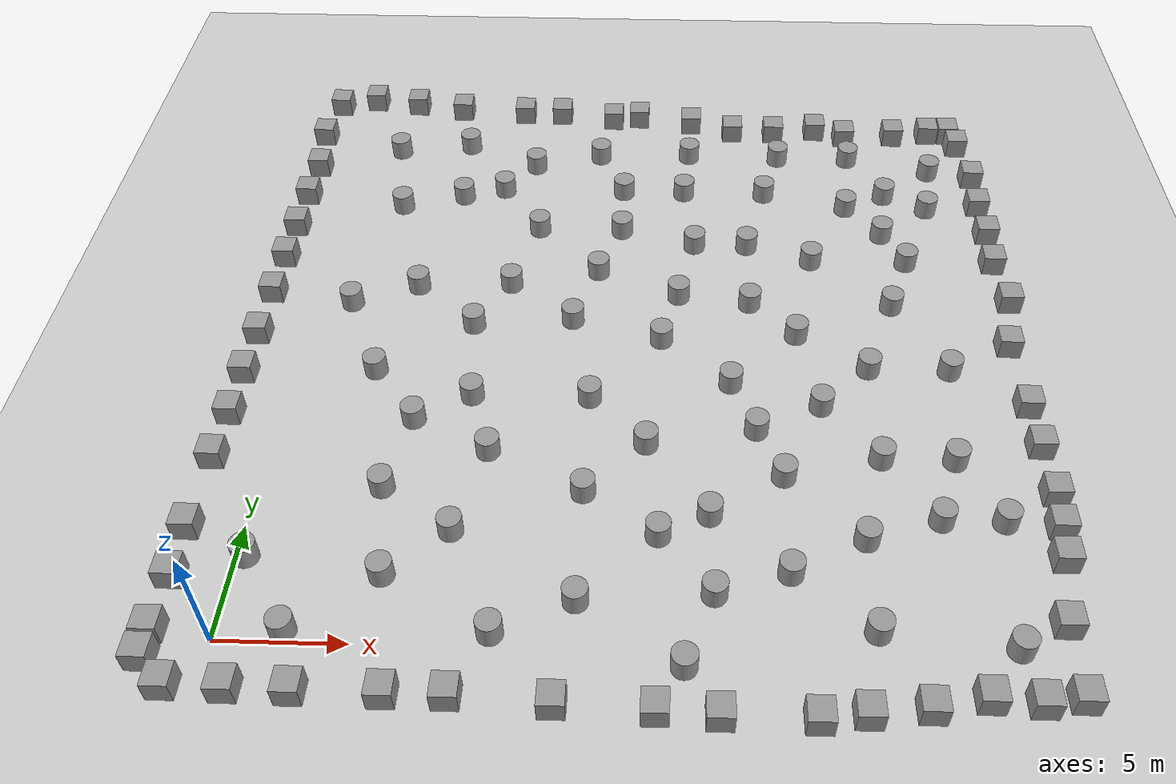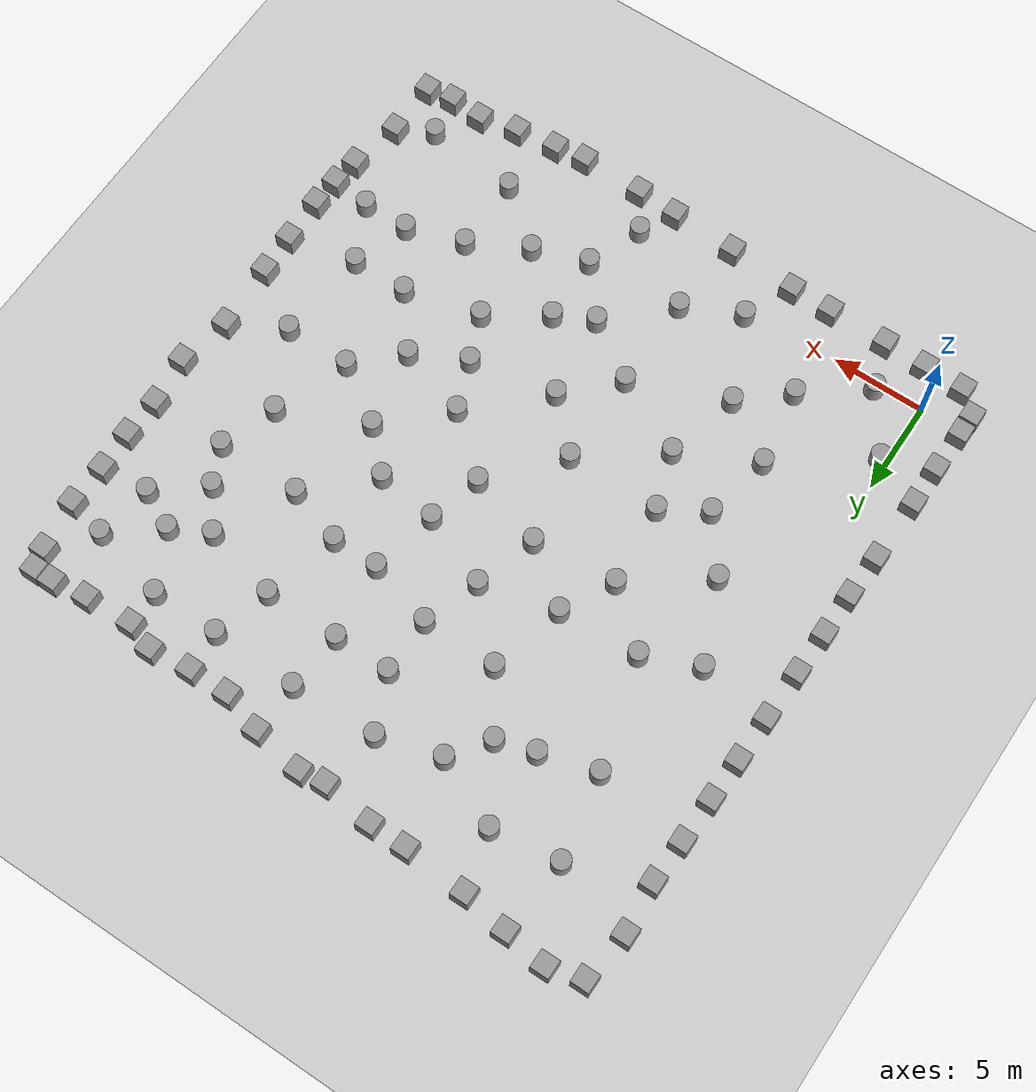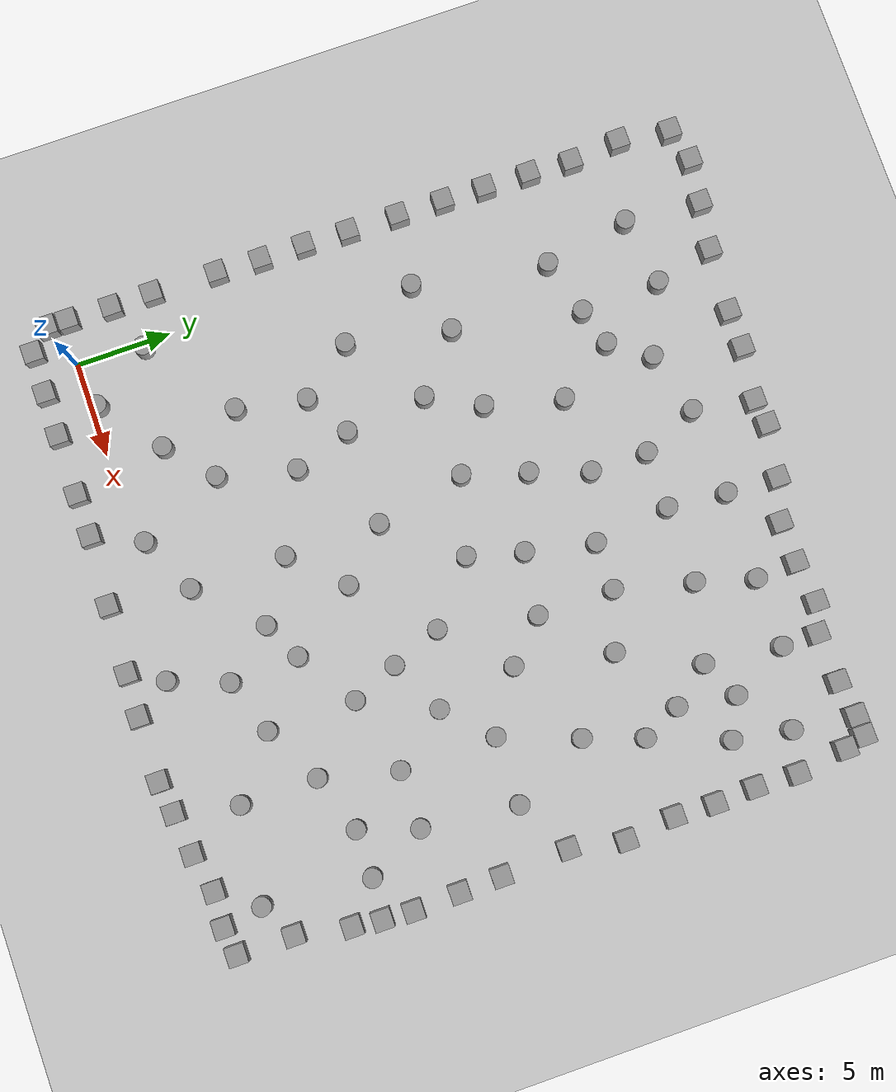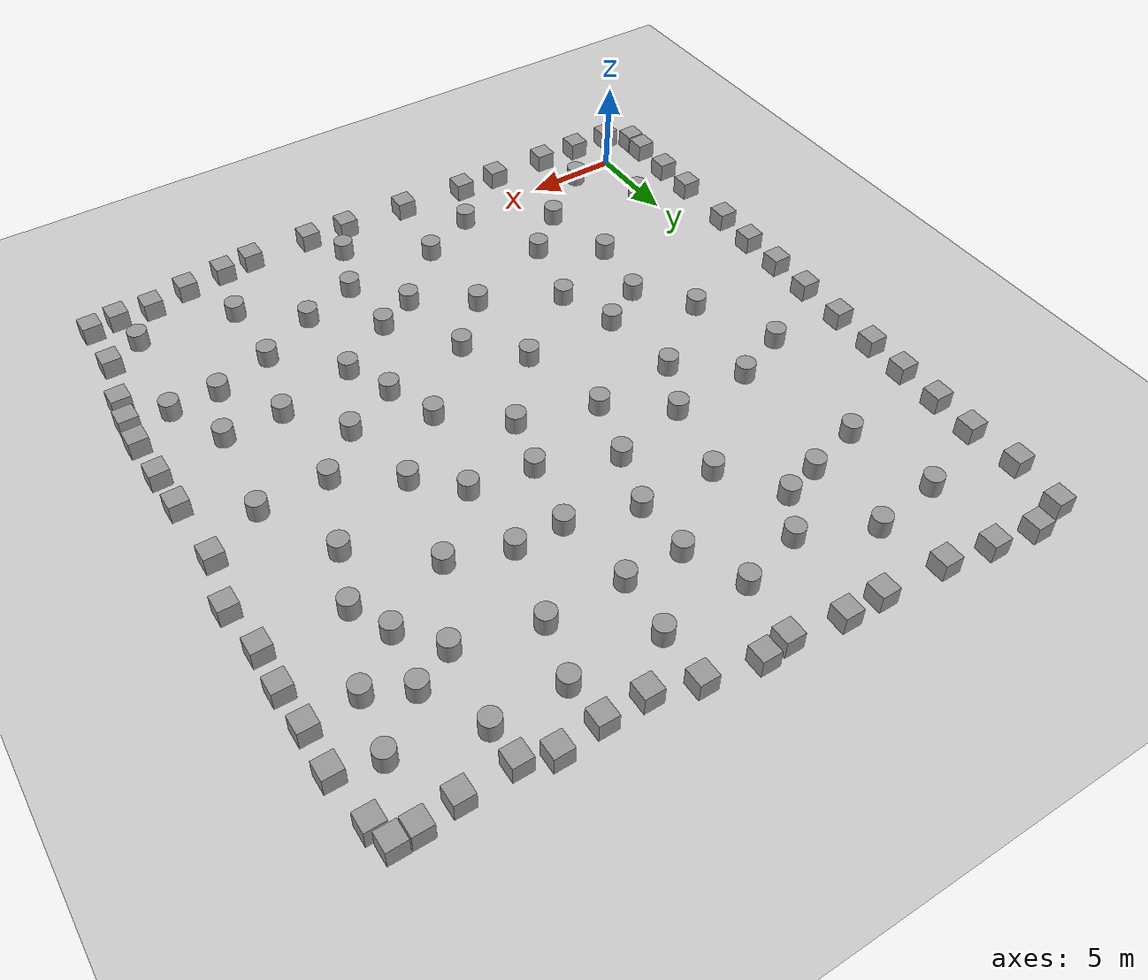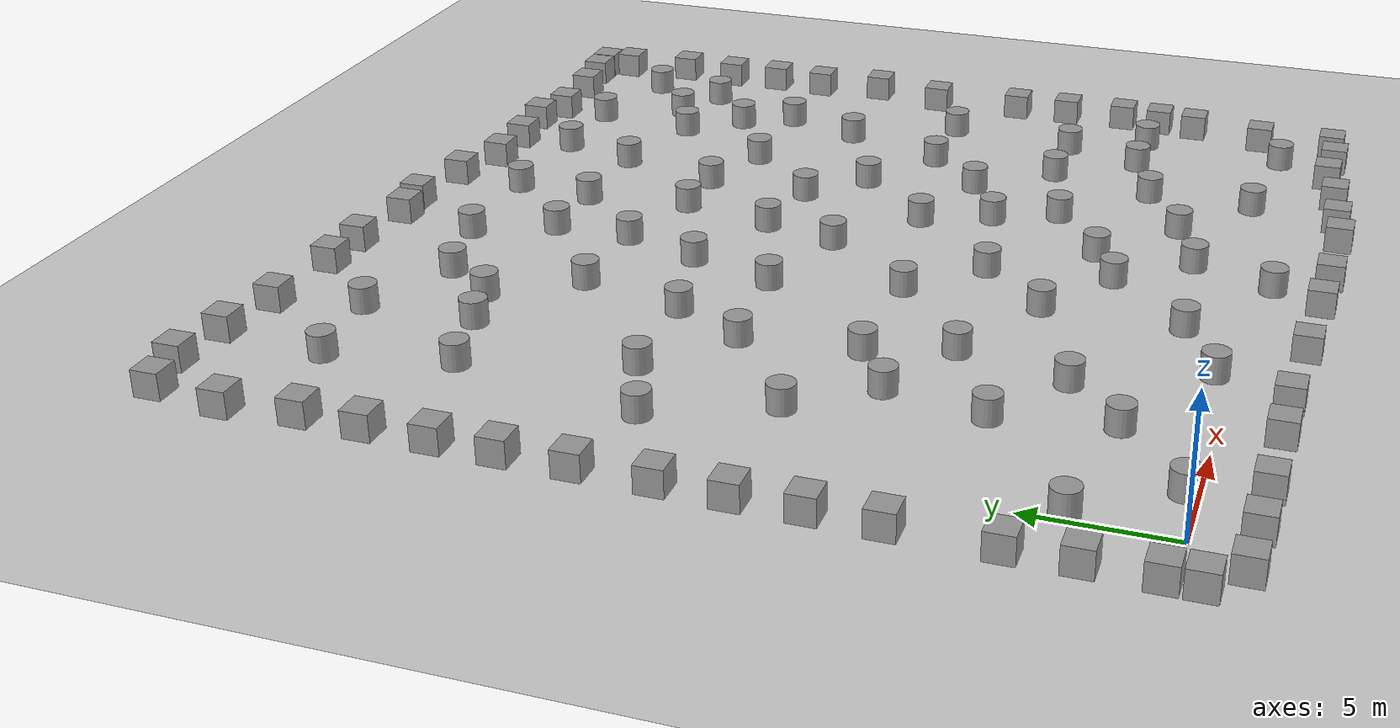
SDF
<sdf version="1.7">
 <world name="default">
  <model name="ground_plane">
   <static>1</static>
   <link name="link">
    <collision name="collision">
     <geometry><plane><normal>0 0 1</normal><size>100 100</size></plane></geometry>
     <surface><friction><ode><mu>100</mu><mu2>50</mu2></ode></friction></surface>
    </collision>
    <visual name="visual">
     <cast_shadows>0</cast_shadows>
     <geometry><plane><normal>0 0 1</normal><size>100 100</size></plane></geometry>
     <material>
      <script><uri>file://media/materials/scripts/gazebo.material</uri><name>Gazebo/Grey</name></script>
     </material>
    </visual>
   </link>
  </model>
  <light name="sun" type="directional">
   <pose>0 0 10 0 -0 0</pose>
   <diffuse>0.8 0.8 0.8 1</diffuse>
   <specular>0.2 0.2 0.2 1</specular>
   <attenuation>
    <range>1000</range>
    <constant>0.9</constant>
    <linear>0.01</linear>
    <quadratic>0.001</quadratic>
   </attenuation>
   <direction>-0.5 0.1 -0.9</direction>
   <spot><inner_angle>0</inner_angle><outer_angle>0</outer_angle><falloff>0</falloff></spot>
  </light>
  <gravity>0 0 -9.8</gravity>
  <magnetic_field>6e-06 2.3e-05 -4.2e-05</magnetic_field>
  <atmosphere type="adiabatic"/>
  <physics type="ode">
   <max_step_size>0.001</max_step_size>
   <real_time_factor>1</real_time_factor>
   <real_time_update_rate>1000</real_time_update_rate>
  </physics>
  <scene><ambient>0.4 0.4 0.4 1</ambient><background>0.7 0.7 0.7 1</background><shadows>1</shadows></scene>
  <audio><device>default</device></audio>
  <spherical_coordinates>
   <surface_model>EARTH_WGS84</surface_model>
   <latitude_deg>0</latitude_deg>
   <longitude_deg>0</longitude_deg>
   <elevation>0</elevation>
   <heading_deg>0</heading_deg>
  </spherical_coordinates>
  <model name="unit_box_0">
   <pose>-2.22865 0.326049 0.5 -0 -0 -0</pose>
   <link name="link">
    <inertial>
     <mass>1</mass>
     <inertia>
      <ixx>0.166667</ixx>
      <ixy>0</ixy>
      <ixz>0</ixz>
      <iyy>0.166667</iyy>
      <iyz>0</iyz>
      <izz>0.166667</izz>
     </inertia>
    </inertial>
    <collision name="collision"><geometry><box><size>1 1 1</size></box></geometry></collision>
    <visual name="visual">
     <geometry><box><size>1 1 1</size></box></geometry>
     <material>
      <script><name>Gazebo/Grey</name><uri>file://media/materials/scripts/gazebo.material</uri></script>
     </material>
    </visual>
   </link>
  </model>
  <model name="unit_box_0_clone_0">
   <pose>-2.16445 2.63677 0.5 0 -0 0</pose>
   <link name="link">
    <inertial>
     <mass>1</mass>
     <inertia>
      <ixx>0.166667</ixx>
      <ixy>0</ixy>
      <ixz>0</ixz>
      <iyy>0.166667</iyy>
      <iyz>0</iyz>
      <izz>0.166667</izz>
     </inertia>
    </inertial>
    <collision name="collision"><geometry><box><size>1 1 1</size></box></geometry></collision>
    <visual name="visual">
     <geometry><box><size>1 1 1</size></box></geometry>
     <material>
      <script><name>Gazebo/Grey</name><uri>file://media/materials/scripts/gazebo.material</uri></script>
     </material>
    </visual>
   </link>
  </model>
  <model name="unit_box_0_clone_2">
   <pose>-2.17584 4.83845 0.5 0 -0 0</pose>
   <link name="link">
    <inertial>
     <mass>1</mass>
     <inertia>
      <ixx>0.166667</ixx>
      <ixy>0</ixy>
      <ixz>0</ixz>
      <iyy>0.166667</iyy>
      <iyz>0</iyz>
      <izz>0.166667</izz>
     </inertia>
    </inertial>
    <collision name="collision"><geometry><box><size>1 1 1</size></box></geometry></collision>
    <visual name="visual">
     <geometry><box><size>1 1 1</size></box></geometry>
     <material>
      <script><name>Gazebo/Grey</name><uri>file://media/materials/scripts/gazebo.material</uri></script>
     </material>
    </visual>
   </link>
  </model>
  <model name="unit_box_0_clone_5">
   <pose>-2.11196 8.30155 0.5 0 -0 0</pose>
   <link name="link">
    <inertial>
     <mass>1</mass>
     <inertia>
      <ixx>0.166667</ixx>
      <ixy>0</ixy>
      <ixz>0</ixz>
      <iyy>0.166667</iyy>
      <iyz>0</iyz>
      <izz>0.166667</izz>
     </inertia>
    </inertial>
    <collision name="collision"><geometry><box><size>1 1 1</size></box></geometry></collision>
    <visual name="visual">
     <geometry><box><size>1 1 1</size></box></geometry>
     <material>
      <script><name>Gazebo/Grey</name><uri>file://media/materials/scripts/gazebo.material</uri></script>
     </material>
    </visual>
   </link>
  </model>
  <model name="unit_box_0_clone_7">
   <pose>-2.03622 10.6755 0.5 0 -0 0</pose>
   <link name="link">
    <inertial>
     <mass>1</mass>
     <inertia>
      <ixx>0.166667</ixx>
      <ixy>0</ixy>
      <ixz>0</ixz>
      <iyy>0.166667</iyy>
      <iyz>0</iyz>
      <izz>0.166667</izz>
     </inertia>
    </inertial>
    <collision name="collision"><geometry><box><size>1 1 1</size></box></geometry></collision>
    <visual name="visual">
     <geometry><box><size>1 1 1</size></box></geometry>
     <material>
      <script><name>Gazebo/Grey</name><uri>file://media/materials/scripts/gazebo.material</uri></script>
     </material>
    </visual>
   </link>
  </model>
  <model name="unit_box_0_clone_9">
   <pose>-2.03088 13.0171 0.5 0 -0 0</pose>
   <link name="link">
    <inertial>
     <mass>1</mass>
     <inertia>
      <ixx>0.166667</ixx>
      <ixy>0</ixy>
      <ixz>0</ixz>
      <iyy>0.166667</iyy>
      <iyz>0</iyz>
      <izz>0.166667</izz>
     </inertia>
    </inertial>
    <collision name="collision"><geometry><box><size>1 1 1</size></box></geometry></collision>
    <visual name="visual">
     <geometry><box><size>1 1 1</size></box></geometry>
     <material>
      <script><name>Gazebo/Grey</name><uri>file://media/materials/scripts/gazebo.material</uri></script>
     </material>
    </visual>
   </link>
  </model>
  <model name="unit_box_0_clone_11">
   <pose>-1.97332 15.4004 0.5 0 -0 0</pose>
   <link name="link">
    <inertial>
     <mass>1</mass>
     <inertia>
      <ixx>0.166667</ixx>
      <ixy>0</ixy>
      <ixz>0</ixz>
      <iyy>0.166667</iyy>
      <iyz>0</iyz>
      <izz>0.166667</izz>
     </inertia>
    </inertial>
    <collision name="collision"><geometry><box><size>1 1 1</size></box></geometry></collision>
    <visual name="visual">
     <geometry><box><size>1 1 1</size></box></geometry>
     <material>
      <script><name>Gazebo/Grey</name><uri>file://media/materials/scripts/gazebo.material</uri></script>
     </material>
    </visual>
   </link>
  </model>
  <model name="unit_box_0_clone_13">
   <pose>-1.93409 18.082 0.5 0 -0 0</pose>
   <link name="link">
    <inertial>
     <mass>1</mass>
     <inertia>
      <ixx>0.166667</ixx>
      <ixy>0</ixy>
      <ixz>0</ixz>
      <iyy>0.166667</iyy>
      <iyz>0</iyz>
      <izz>0.166667</izz>
     </inertia>
    </inertial>
    <collision name="collision"><geometry><box><size>1 1 1</size></box></geometry></collision>
    <visual name="visual">
     <geometry><box><size>1 1 1</size></box></geometry>
     <material>
      <script><name>Gazebo/Grey</name><uri>file://media/materials/scripts/gazebo.material</uri></script>
     </material>
    </visual>
   </link>
  </model>
  <model name="unit_box_0_clone_15">
   <pose>-1.90893 20.5485 0.5 0 -0 0</pose>
   <link name="link">
    <inertial>
     <mass>1</mass>
     <inertia>
      <ixx>0.166667</ixx>
      <ixy>0</ixy>
      <ixz>0</ixz>
      <iyy>0.166667</iyy>
      <iyz>0</iyz>
      <izz>0.166667</izz>
     </inertia>
    </inertial>
    <collision name="collision"><geometry><box><size>1 1 1</size></box></geometry></collision>
    <visual name="visual">
     <geometry><box><size>1 1 1</size></box></geometry>
     <material>
      <script><name>Gazebo/Grey</name><uri>file://media/materials/scripts/gazebo.material</uri></script>
     </material>
    </visual>
   </link>
  </model>
  <model name="unit_box_0_clone_17">
   <pose>-1.85948 22.8232 0.5 0 -0 0</pose>
   <link name="link">
    <inertial>
     <mass>1</mass>
     <inertia>
      <ixx>0.166667</ixx>
      <ixy>0</ixy>
      <ixz>0</ixz>
      <iyy>0.166667</iyy>
      <iyz>0</iyz>
      <izz>0.166667</izz>
     </inertia>
    </inertial>
    <collision name="collision"><geometry><box><size>1 1 1</size></box></geometry></collision>
    <visual name="visual">
     <geometry><box><size>1 1 1</size></box></geometry>
     <material>
      <script><name>Gazebo/Grey</name><uri>file://media/materials/scripts/gazebo.material</uri></script>
     </material>
    </visual>
   </link>
  </model>
  <model name="unit_box_0_clone_19">
   <pose>-1.81419 25.2248 0.5 0 -0 0</pose>
   <link name="link">
    <inertial>
     <mass>1</mass>
     <inertia>
      <ixx>0.166667</ixx>
      <ixy>0</ixy>
      <ixz>0</ixz>
      <iyy>0.166667</iyy>
      <iyz>0</iyz>
      <izz>0.166667</izz>
     </inertia>
    </inertial>
    <collision name="collision"><geometry><box><size>1 1 1</size></box></geometry></collision>
    <visual name="visual">
     <geometry><box><size>1 1 1</size></box></geometry>
     <material>
      <script><name>Gazebo/Grey</name><uri>file://media/materials/scripts/gazebo.material</uri></script>
     </material>
    </visual>
   </link>
  </model>
  <model name="unit_box_0_clone_21">
   <pose>-1.71241 27.5404 0.5 0 -0 0</pose>
   <link name="link">
    <inertial>
     <mass>1</mass>
     <inertia>
      <ixx>0.166667</ixx>
      <ixy>0</ixy>
      <ixz>0</ixz>
      <iyy>0.166667</iyy>
      <iyz>0</iyz>
      <izz>0.166667</izz>
     </inertia>
    </inertial>
    <collision name="collision"><geometry><box><size>1 1 1</size></box></geometry></collision>
    <visual name="visual">
     <geometry><box><size>1 1 1</size></box></geometry>
     <material>
      <script><name>Gazebo/Grey</name><uri>file://media/materials/scripts/gazebo.material</uri></script>
     </material>
    </visual>
   </link>
  </model>
  <model name="unit_box_0_clone_22">
   <pose>-2.24379 -0.772102 0.5 0 -0 0</pose>
   <link name="link">
    <inertial>
     <mass>1</mass>
     <inertia>
      <ixx>0.166667</ixx>
      <ixy>0</ixy>
      <ixz>0</ixz>
      <iyy>0.166667</iyy>
      <iyz>0</iyz>
      <izz>0.166667</izz>
     </inertia>
    </inertial>
    <collision name="collision"><geometry><box><size>1 1 1</size></box></geometry></collision>
    <visual name="visual">
     <geometry><box><size>1 1 1</size></box></geometry>
     <material>
      <script><name>Gazebo/Grey</name><uri>file://media/materials/scripts/gazebo.material</uri></script>
     </material>
    </visual>
   </link>
  </model>
  <model name="unit_box_0_clone_23">
   <pose>-1.13961 -1.85818 0.5 0 -0 0</pose>
   <link name="link">
    <inertial>
     <mass>1</mass>
     <inertia>
      <ixx>0.166667</ixx>
      <ixy>0</ixy>
      <ixz>0</ixz>
      <iyy>0.166667</iyy>
      <iyz>0</iyz>
      <izz>0.166667</izz>
     </inertia>
    </inertial>
    <collision name="collision"><geometry><box><size>1 1 1</size></box></geometry></collision>
    <visual name="visual">
     <geometry><box><size>1 1 1</size></box></geometry>
     <material>
      <script><name>Gazebo/Grey</name><uri>file://media/materials/scripts/gazebo.material</uri></script>
     </material>
    </visual>
   </link>
  </model>
  <model name="unit_box_0_clone_25">
   <pose>1.04752 -1.90962 0.5 0 -0 0</pose>
   <link name="link">
    <inertial>
     <mass>1</mass>
     <inertia>
      <ixx>0.166667</ixx>
      <ixy>0</ixy>
      <ixz>0</ixz>
      <iyy>0.166667</iyy>
      <iyz>0</iyz>
      <izz>0.166667</izz>
     </inertia>
    </inertial>
    <collision name="collision"><geometry><box><size>1 1 1</size></box></geometry></collision>
    <visual name="visual">
     <geometry><box><size>1 1 1</size></box></geometry>
     <material>
      <script><name>Gazebo/Grey</name><uri>file://media/materials/scripts/gazebo.material</uri></script>
     </material>
    </visual>
   </link>
  </model>
  <model name="unit_box_0_clone_27">
   <pose>3.34569 -1.94663 0.5 0 -0 0</pose>
   <link name="link">
    <inertial>
     <mass>1</mass>
     <inertia>
      <ixx>0.166667</ixx>
      <ixy>0</ixy>
      <ixz>0</ixz>
      <iyy>0.166667</iyy>
      <iyz>0</iyz>
      <izz>0.166667</izz>
     </inertia>
    </inertial>
    <collision name="collision"><geometry><box><size>1 1 1</size></box></geometry></collision>
    <visual name="visual">
     <geometry><box><size>1 1 1</size></box></geometry>
     <material>
      <script><name>Gazebo/Grey</name><uri>file://media/materials/scripts/gazebo.material</uri></script>
     </material>
    </visual>
   </link>
  </model>
  <model name="unit_box_0_clone_27_clone_1">
   <pose>6.55096 -1.97487 0.5 0 -0 0</pose>
   <link name="link">
    <inertial>
     <mass>1</mass>
     <inertia>
      <ixx>0.166667</ixx>
      <ixy>0</ixy>
      <ixz>0</ixz>
      <iyy>0.166667</iyy>
      <iyz>0</iyz>
      <izz>0.166667</izz>
     </inertia>
    </inertial>
    <collision name="collision"><geometry><box><size>1 1 1</size></box></geometry></collision>
    <visual name="visual">
     <geometry><box><size>1 1 1</size></box></geometry>
     <material>
      <script><name>Gazebo/Grey</name><uri>file://media/materials/scripts/gazebo.material</uri></script>
     </material>
    </visual>
   </link>
  </model>
  <model name="unit_box_0_clone_27_clone_3">
   <pose>8.77506 -1.97155 0.5 0 -0 0</pose>
   <link name="link">
    <inertial>
     <mass>1</mass>
     <inertia>
      <ixx>0.166667</ixx>
      <ixy>0</ixy>
      <ixz>0</ixz>
      <iyy>0.166667</iyy>
      <iyz>0</iyz>
      <izz>0.166667</izz>
     </inertia>
    </inertial>
    <collision name="collision"><geometry><box><size>1 1 1</size></box></geometry></collision>
    <visual name="visual">
     <geometry><box><size>1 1 1</size></box></geometry>
     <material>
      <script><name>Gazebo/Grey</name><uri>file://media/materials/scripts/gazebo.material</uri></script>
     </material>
    </visual>
   </link>
  </model>
  <model name="unit_box_0_clone_27_clone_6">
   <pose>12.4447 -2.18446 0.5 0 -0 0</pose>
   <link name="link">
    <inertial>
     <mass>1</mass>
     <inertia>
      <ixx>0.166667</ixx>
      <ixy>0</ixy>
      <ixz>0</ixz>
      <iyy>0.166667</iyy>
      <iyz>0</iyz>
      <izz>0.166667</izz>
     </inertia>
    </inertial>
    <collision name="collision"><geometry><box><size>1 1 1</size></box></geometry></collision>
    <visual name="visual">
     <geometry><box><size>1 1 1</size></box></geometry>
     <material>
      <script><name>Gazebo/Grey</name><uri>file://media/materials/scripts/gazebo.material</uri></script>
     </material>
    </visual>
   </link>
  </model>
  <model name="unit_box_0_clone_27_clone_9">
   <pose>15.99 -2.33679 0.5 0 -0 0</pose>
   <link name="link">
    <inertial>
     <mass>1</mass>
     <inertia>
      <ixx>0.166667</ixx>
      <ixy>0</ixy>
      <ixz>0</ixz>
      <iyy>0.166667</iyy>
      <iyz>0</iyz>
      <izz>0.166667</izz>
     </inertia>
    </inertial>
    <collision name="collision"><geometry><box><size>1 1 1</size></box></geometry></collision>
    <visual name="visual">
     <geometry><box><size>1 1 1</size></box></geometry>
     <material>
      <script><name>Gazebo/Grey</name><uri>file://media/materials/scripts/gazebo.material</uri></script>
     </material>
    </visual>
   </link>
  </model>
  <model name="unit_box_0_clone_27_clone_11">
   <pose>18.2224 -2.44772 0.5 0 -0 0</pose>
   <link name="link">
    <inertial>
     <mass>1</mass>
     <inertia>
      <ixx>0.166667</ixx>
      <ixy>0</ixy>
      <ixz>0</ixz>
      <iyy>0.166667</iyy>
      <iyz>0</iyz>
      <izz>0.166667</izz>
     </inertia>
    </inertial>
    <collision name="collision"><geometry><box><size>1 1 1</size></box></geometry></collision>
    <visual name="visual">
     <geometry><box><size>1 1 1</size></box></geometry>
     <material>
      <script><name>Gazebo/Grey</name><uri>file://media/materials/scripts/gazebo.material</uri></script>
     </material>
    </visual>
   </link>
  </model>
  <model name="unit_box">
   <pose>19.5582 31.1273 0.5 -0 -0 -0</pose>
   <link name="link">
    <inertial>
     <mass>1</mass>
     <inertia>
      <ixx>0.166667</ixx>
      <ixy>0</ixy>
      <ixz>0</ixz>
      <iyy>0.166667</iyy>
      <iyz>0</iyz>
      <izz>0.166667</izz>
     </inertia>
    </inertial>
    <collision name="collision"><geometry><box><size>1 1 1</size></box></geometry></collision>
    <visual name="visual">
     <geometry><box><size>1 1 1</size></box></geometry>
     <material>
      <script><name>Gazebo/Grey</name><uri>file://media/materials/scripts/gazebo.material</uri></script>
     </material>
    </visual>
   </link>
  </model>
  <model name="unit_box_1">
   <pose>13.2418 32.0764 0.5 -0 -0 -0</pose>
   <link name="link">
    <inertial>
     <mass>1</mass>
     <inertia>
      <ixx>0.166667</ixx>
      <ixy>0</ixy>
      <ixz>0</ixz>
      <iyy>0.166667</iyy>
      <iyz>0</iyz>
      <izz>0.166667</izz>
     </inertia>
    </inertial>
    <collision name="collision"><geometry><box><size>1 1 1</size></box></geometry></collision>
    <visual name="visual">
     <geometry><box><size>1 1 1</size></box></geometry>
     <material>
      <script><name>Gazebo/Grey</name><uri>file://media/materials/scripts/gazebo.material</uri></script>
     </material>
    </visual>
   </link>
  </model>
  <model name="unit_box_2">
   <pose>8.46351 32.48 0.5 -0 -0 -0</pose>
   <link name="link">
    <inertial>
     <mass>1</mass>
     <inertia>
      <ixx>0.166667</ixx>
      <ixy>0</ixy>
      <ixz>0</ixz>
      <iyy>0.166667</iyy>
      <iyz>0</iyz>
      <izz>0.166667</izz>
     </inertia>
    </inertial>
    <collision name="collision"><geometry><box><size>1 1 1</size></box></geometry></collision>
    <visual name="visual">
     <geometry><box><size>1 1 1</size></box></geometry>
     <material>
      <script><name>Gazebo/Grey</name><uri>file://media/materials/scripts/gazebo.material</uri></script>
     </material>
    </visual>
   </link>
  </model>
  <model name="unit_box_3">
   <pose>10.4591 32.4738 0.5 -0 -0 -0</pose>
   <link name="link">
    <inertial>
     <mass>1</mass>
     <inertia>
      <ixx>0.166667</ixx>
      <ixy>0</ixy>
      <ixz>0</ixz>
      <iyy>0.166667</iyy>
      <iyz>0</iyz>
      <izz>0.166667</izz>
     </inertia>
    </inertial>
    <collision name="collision"><geometry><box><size>1 1 1</size></box></geometry></collision>
    <visual name="visual">
     <geometry><box><size>1 1 1</size></box></geometry>
     <material>
      <script><name>Gazebo/Grey</name><uri>file://media/materials/scripts/gazebo.material</uri></script>
     </material>
    </visual>
   </link>
  </model>
  <model name="unit_box_4">
   <pose>5.07451 32.7008 0.5 -0 -0 -0</pose>
   <link name="link">
    <inertial>
     <mass>1</mass>
     <inertia>
      <ixx>0.166667</ixx>
      <ixy>0</ixy>
      <ixz>0</ixz>
      <iyy>0.166667</iyy>
      <iyz>0</iyz>
      <izz>0.166667</izz>
     </inertia>
    </inertial>
    <collision name="collision"><geometry><box><size>1 1 1</size></box></geometry></collision>
    <visual name="visual">
     <geometry><box><size>1 1 1</size></box></geometry>
     <material>
      <script><name>Gazebo/Grey</name><uri>file://media/materials/scripts/gazebo.material</uri></script>
     </material>
    </visual>
   </link>
  </model>
  <model name="unit_box_5">
   <pose>2.57079 33.0945 0.5 -0 -0 -0</pose>
   <link name="link">
    <inertial>
     <mass>1</mass>
     <inertia>
      <ixx>0.166667</ixx>
      <ixy>0</ixy>
      <ixz>0</ixz>
      <iyy>0.166667</iyy>
      <iyz>0</iyz>
      <izz>0.166667</izz>
     </inertia>
    </inertial>
    <collision name="collision"><geometry><box><size>1 1 1</size></box></geometry></collision>
    <visual name="visual">
     <geometry><box><size>1 1 1</size></box></geometry>
     <material>
      <script><name>Gazebo/Grey</name><uri>file://media/materials/scripts/gazebo.material</uri></script>
     </material>
    </visual>
   </link>
  </model>
  <model name="unit_box_6">
   <pose>0.246513 33.4093 0.5 -0 -0 -0</pose>
   <link name="link">
    <inertial>
     <mass>1</mass>
     <inertia>
      <ixx>0.166667</ixx>
      <ixy>0</ixy>
      <ixz>0</ixz>
      <iyy>0.166667</iyy>
      <iyz>0</iyz>
      <izz>0.166667</izz>
     </inertia>
    </inertial>
    <collision name="collision"><geometry><box><size>1 1 1</size></box></geometry></collision>
    <visual name="visual">
     <geometry><box><size>1 1 1</size></box></geometry>
     <material>
      <script><name>Gazebo/Grey</name><uri>file://media/materials/scripts/gazebo.material</uri></script>
     </material>
    </visual>
   </link>
  </model>
  <model name="unit_box_7">
   <pose>-1.58382 32.9418 0.5 -0 -0 -0</pose>
   <link name="link">
    <inertial>
     <mass>1</mass>
     <inertia>
      <ixx>0.166667</ixx>
      <ixy>0</ixy>
      <ixz>0</ixz>
      <iyy>0.166667</iyy>
      <iyz>0</iyz>
      <izz>0.166667</izz>
     </inertia>
    </inertial>
    <collision name="collision"><geometry><box><size>1 1 1</size></box></geometry></collision>
    <visual name="visual">
     <geometry><box><size>1 1 1</size></box></geometry>
     <material>
      <script><name>Gazebo/Grey</name><uri>file://media/materials/scripts/gazebo.material</uri></script>
     </material>
    </visual>
   </link>
  </model>
  <model name="unit_box_8">
   <pose>-1.95351 30.2154 0.5 -0 -0 -0</pose>
   <link name="link">
    <inertial>
     <mass>1</mass>
     <inertia>
      <ixx>0.166667</ixx>
      <ixy>0</ixy>
      <ixz>0</ixz>
      <iyy>0.166667</iyy>
      <iyz>0</iyz>
      <izz>0.166667</izz>
     </inertia>
    </inertial>
    <collision name="collision"><geometry><box><size>1 1 1</size></box></geometry></collision>
    <visual name="visual">
     <geometry><box><size>1 1 1</size></box></geometry>
     <material>
      <script><name>Gazebo/Grey</name><uri>file://media/materials/scripts/gazebo.material</uri></script>
     </material>
    </visual>
   </link>
  </model>
  <model name="unit_box_9">
   <pose>25.4229 30.8816 0.5 -0 -0 -0</pose>
   <link name="link">
    <inertial>
     <mass>1</mass>
     <inertia>
      <ixx>0.166667</ixx>
      <ixy>0</ixy>
      <ixz>0</ixz>
      <iyy>0.166667</iyy>
      <iyz>0</iyz>
      <izz>0.166667</izz>
     </inertia>
    </inertial>
    <collision name="collision"><geometry><box><size>1 1 1</size></box></geometry></collision>
    <visual name="visual">
     <geometry><box><size>1 1 1</size></box></geometry>
     <material>
      <script><name>Gazebo/Grey</name><uri>file://media/materials/scripts/gazebo.material</uri></script>
     </material>
    </visual>
   </link>
  </model>
  <model name="unit_box_11">
   <pose>21.5967 -2.48668 0.5 -0 -0 -0</pose>
   <link name="link">
    <inertial>
     <mass>1</mass>
     <inertia>
      <ixx>0.166667</ixx>
      <ixy>0</ixy>
      <ixz>0</ixz>
      <iyy>0.166667</iyy>
      <iyz>0</iyz>
      <izz>0.166667</izz>
     </inertia>
    </inertial>
    <collision name="collision"><geometry><box><size>1 1 1</size></box></geometry></collision>
    <visual name="visual">
     <geometry><box><size>1 1 1</size></box></geometry>
     <material>
      <script><name>Gazebo/Grey</name><uri>file://media/materials/scripts/gazebo.material</uri></script>
     </material>
    </visual>
   </link>
  </model>
  <model name="unit_box_12">
   <pose>23.2882 -2.25784 0.5 -0 -0 -0</pose>
   <link name="link">
    <inertial>
     <mass>1</mass>
     <inertia>
      <ixx>0.166667</ixx>
      <ixy>0</ixy>
      <ixz>0</ixz>
      <iyy>0.166667</iyy>
      <iyz>0</iyz>
      <izz>0.166667</izz>
     </inertia>
    </inertial>
    <collision name="collision"><geometry><box><size>1 1 1</size></box></geometry></collision>
    <visual name="visual">
     <geometry><box><size>1 1 1</size></box></geometry>
     <material>
      <script><name>Gazebo/Grey</name><uri>file://media/materials/scripts/gazebo.material</uri></script>
     </material>
    </visual>
   </link>
  </model>
  <model name="unit_box_13">
   <pose>30.7878 -1.46301 0.5 0 -0 0</pose>
   <link name="link">
    <inertial>
     <mass>1</mass>
     <inertia>
      <ixx>0.166667</ixx>
      <ixy>0</ixy>
      <ixz>0</ixz>
      <iyy>0.166667</iyy>
      <iyz>0</iyz>
      <izz>0.166667</izz>
     </inertia>
    </inertial>
    <collision name="collision"><geometry><box><size>1 1 1</size></box></geometry></collision>
    <visual name="visual">
     <geometry><box><size>1 1 1</size></box></geometry>
     <material>
      <script><name>Gazebo/Grey</name><uri>file://media/materials/scripts/gazebo.material</uri></script>
     </material>
    </visual>
   </link>
  </model>
  <model name="unit_box_14">
   <pose>30.8153 1.4746 0.5 0 -0 0</pose>
   <link name="link">
    <inertial>
     <mass>1</mass>
     <inertia>
      <ixx>0.166667</ixx>
      <ixy>0</ixy>
      <ixz>0</ixz>
      <iyy>0.166667</iyy>
      <iyz>0</iyz>
      <izz>0.166667</izz>
     </inertia>
    </inertial>
    <collision name="collision"><geometry><box><size>1 1 1</size></box></geometry></collision>
    <visual name="visual">
     <geometry><box><size>1 1 1</size></box></geometry>
     <material>
      <script><name>Gazebo/Grey</name><uri>file://media/materials/scripts/gazebo.material</uri></script>
     </material>
    </visual>
   </link>
  </model>
  <model name="unit_box_15">
   <pose>31.3664 4.30408 0.5 0 -0 0</pose>
   <link name="link">
    <inertial>
     <mass>1</mass>
     <inertia>
      <ixx>0.166667</ixx>
      <ixy>0</ixy>
      <ixz>0</ixz>
      <iyy>0.166667</iyy>
      <iyz>0</iyz>
      <izz>0.166667</izz>
     </inertia>
    </inertial>
    <collision name="collision"><geometry><box><size>1 1 1</size></box></geometry></collision>
    <visual name="visual">
     <geometry><box><size>1 1 1</size></box></geometry>
     <material>
      <script><name>Gazebo/Grey</name><uri>file://media/materials/scripts/gazebo.material</uri></script>
     </material>
    </visual>
   </link>
  </model>
  <model name="unit_box_16">
   <pose>31.6348 7.37884 0.5 0 -0 0</pose>
   <link name="link">
    <inertial>
     <mass>1</mass>
     <inertia>
      <ixx>0.166667</ixx>
      <ixy>0</ixy>
      <ixz>0</ixz>
      <iyy>0.166667</iyy>
      <iyz>0</iyz>
      <izz>0.166667</izz>
     </inertia>
    </inertial>
    <collision name="collision"><geometry><box><size>1 1 1</size></box></geometry></collision>
    <visual name="visual">
     <geometry><box><size>1 1 1</size></box></geometry>
     <material>
      <script><name>Gazebo/Grey</name><uri>file://media/materials/scripts/gazebo.material</uri></script>
     </material>
    </visual>
   </link>
  </model>
  <model name="unit_box_16_clone">
   <pose>31.5578 9.79822 0.5 -0 -0 -0</pose>
   <link name="link">
    <inertial>
     <mass>1</mass>
     <inertia>
      <ixx>0.166667</ixx>
      <ixy>0</ixy>
      <ixz>0</ixz>
      <iyy>0.166667</iyy>
      <iyz>0</iyz>
      <izz>0.166667</izz>
     </inertia>
    </inertial>
    <collision name="collision"><geometry><box><size>1 1 1</size></box></geometry></collision>
    <visual name="visual">
     <geometry><box><size>1 1 1</size></box></geometry>
     <material>
      <script><name>Gazebo/Grey</name><uri>file://media/materials/scripts/gazebo.material</uri></script>
     </material>
    </visual>
   </link>
  </model>
  <model name="unit_box_16_clone_0">
   <pose>31.4869 12 0.5 -0 -0 -0</pose>
   <link name="link">
    <inertial>
     <mass>1</mass>
     <inertia>
      <ixx>0.166667</ixx>
      <ixy>0</ixy>
      <ixz>0</ixz>
      <iyy>0.166667</iyy>
      <iyz>0</iyz>
      <izz>0.166667</izz>
     </inertia>
    </inertial>
    <collision name="collision"><geometry><box><size>1 1 1</size></box></geometry></collision>
    <visual name="visual">
     <geometry><box><size>1 1 1</size></box></geometry>
     <material>
      <script><name>Gazebo/Grey</name><uri>file://media/materials/scripts/gazebo.material</uri></script>
     </material>
    </visual>
   </link>
  </model>
  <model name="unit_box_16_clone_1">
   <pose>31.3106 15.5427 0.5 -0 -0 -0</pose>
   <link name="link">
    <inertial>
     <mass>1</mass>
     <inertia>
      <ixx>0.166667</ixx>
      <ixy>0</ixy>
      <ixz>0</ixz>
      <iyy>0.166667</iyy>
      <iyz>0</iyz>
      <izz>0.166667</izz>
     </inertia>
    </inertial>
    <collision name="collision"><geometry><box><size>1 1 1</size></box></geometry></collision>
    <visual name="visual">
     <geometry><box><size>1 1 1</size></box></geometry>
     <material>
      <script><name>Gazebo/Grey</name><uri>file://media/materials/scripts/gazebo.material</uri></script>
     </material>
    </visual>
   </link>
  </model>
  <model name="unit_box_16_clone_2">
   <pose>31.8597 18.3744 0.5 0 -0 0</pose>
   <link name="link">
    <inertial>
     <mass>1</mass>
     <inertia>
      <ixx>0.166667</ixx>
      <ixy>0</ixy>
      <ixz>0</ixz>
      <iyy>0.166667</iyy>
      <iyz>0</iyz>
      <izz>0.166667</izz>
     </inertia>
    </inertial>
    <collision name="collision"><geometry><box><size>1 1 1</size></box></geometry></collision>
    <visual name="visual">
     <geometry><box><size>1 1 1</size></box></geometry>
     <material>
      <script><name>Gazebo/Grey</name><uri>file://media/materials/scripts/gazebo.material</uri></script>
     </material>
    </visual>
   </link>
  </model>
  <model name="unit_box_16_clone_3">
   <pose>31.5558 21 0.5 0 -0 0</pose>
   <link name="link">
    <inertial>
     <mass>1</mass>
     <inertia>
      <ixx>0.166667</ixx>
      <ixy>0</ixy>
      <ixz>0</ixz>
      <iyy>0.166667</iyy>
      <iyz>0</iyz>
      <izz>0.166667</izz>
     </inertia>
    </inertial>
    <collision name="collision"><geometry><box><size>1 1 1</size></box></geometry></collision>
    <visual name="visual">
     <geometry><box><size>1 1 1</size></box></geometry>
     <material>
      <script><name>Gazebo/Grey</name><uri>file://media/materials/scripts/gazebo.material</uri></script>
     </material>
    </visual>
   </link>
  </model>
  <model name="unit_box_16_clone_4">
   <pose>31.6287 23.1382 0.5 -0 -0 -0</pose>
   <link name="link">
    <inertial>
     <mass>1</mass>
     <inertia>
      <ixx>0.166667</ixx>
      <ixy>0</ixy>
      <ixz>0</ixz>
      <iyy>0.166667</iyy>
      <iyz>0</iyz>
      <izz>0.166667</izz>
     </inertia>
    </inertial>
    <collision name="collision"><geometry><box><size>1 1 1</size></box></geometry></collision>
    <visual name="visual">
     <geometry><box><size>1 1 1</size></box></geometry>
     <material>
      <script><name>Gazebo/Grey</name><uri>file://media/materials/scripts/gazebo.material</uri></script>
     </material>
    </visual>
   </link>
  </model>
  <model name="unit_box_16_clone_5">
   <pose>31.5315 25.2557 0.5 0 -0 0</pose>
   <link name="link">
    <inertial>
     <mass>1</mass>
     <inertia>
      <ixx>0.166667</ixx>
      <ixy>0</ixy>
      <ixz>0</ixz>
      <iyy>0.166667</iyy>
      <iyz>0</iyz>
      <izz>0.166667</izz>
     </inertia>
    </inertial>
    <collision name="collision"><geometry><box><size>1 1 1</size></box></geometry></collision>
    <visual name="visual">
     <geometry><box><size>1 1 1</size></box></geometry>
     <material>
      <script><name>Gazebo/Grey</name><uri>file://media/materials/scripts/gazebo.material</uri></script>
     </material>
    </visual>
   </link>
  </model>
  <model name="unit_box_16_clone_6">
   <pose>31.5969 27.5166 0.5 0 -0 0</pose>
   <link name="link">
    <inertial>
     <mass>1</mass>
     <inertia>
      <ixx>0.166667</ixx>
      <ixy>0</ixy>
      <ixz>0</ixz>
      <iyy>0.166667</iyy>
      <iyz>0</iyz>
      <izz>0.166667</izz>
     </inertia>
    </inertial>
    <collision name="collision"><geometry><box><size>1 1 1</size></box></geometry></collision>
    <visual name="visual">
     <geometry><box><size>1 1 1</size></box></geometry>
     <material>
      <script><name>Gazebo/Grey</name><uri>file://media/materials/scripts/gazebo.material</uri></script>
     </material>
    </visual>
   </link>
  </model>
  <model name="unit_box_16_clone_7">
   <pose>31.2341 30.1775 0.5 0 -0 0</pose>
   <link name="link">
    <inertial>
     <mass>1</mass>
     <inertia>
      <ixx>0.166667</ixx>
      <ixy>0</ixy>
      <ixz>0</ixz>
      <iyy>0.166667</iyy>
      <iyz>0</iyz>
      <izz>0.166667</izz>
     </inertia>
    </inertial>
    <collision name="collision"><geometry><box><size>1 1 1</size></box></geometry></collision>
    <visual name="visual">
     <geometry><box><size>1 1 1</size></box></geometry>
     <material>
      <script><name>Gazebo/Grey</name><uri>file://media/materials/scripts/gazebo.material</uri></script>
     </material>
    </visual>
   </link>
  </model>
  <model name="unit_box_16_clone_8">
   <pose>30.922 31.2536 0.5 -0 -0 -0</pose>
   <link name="link">
    <inertial>
     <mass>1</mass>
     <inertia>
      <ixx>0.166667</ixx>
      <ixy>0</ixy>
      <ixz>0</ixz>
      <iyy>0.166667</iyy>
      <iyz>0</iyz>
      <izz>0.166667</izz>
     </inertia>
    </inertial>
    <collision name="collision"><geometry><box><size>1 1 1</size></box></geometry></collision>
    <visual name="visual">
     <geometry><box><size>1 1 1</size></box></geometry>
     <material>
      <script><name>Gazebo/Grey</name><uri>file://media/materials/scripts/gazebo.material</uri></script>
     </material>
    </visual>
   </link>
  </model>
  <model name="unit_box_16_clone_9">
   <pose>29.8641 31.2435 0.5 0 -0 0</pose>
   <link name="link">
    <inertial>
     <mass>1</mass>
     <inertia>
      <ixx>0.166667</ixx>
      <ixy>0</ixy>
      <ixz>0</ixz>
      <iyy>0.166667</iyy>
      <iyz>0</iyz>
      <izz>0.166667</izz>
     </inertia>
    </inertial>
    <collision name="collision"><geometry><box><size>1 1 1</size></box></geometry></collision>
    <visual name="visual">
     <geometry><box><size>1 1 1</size></box></geometry>
     <material>
      <script><name>Gazebo/Grey</name><uri>file://media/materials/scripts/gazebo.material</uri></script>
     </material>
    </visual>
   </link>
  </model>
  <model name="unit_box_16_clone_10">
   <pose>28 31 0.5 -0 -0 -0</pose>
   <link name="link">
    <inertial>
     <mass>1</mass>
     <inertia>
      <ixx>0.166667</ixx>
      <ixy>0</ixy>
      <ixz>0</ixz>
      <iyy>0.166667</iyy>
      <iyz>0</iyz>
      <izz>0.166667</izz>
     </inertia>
    </inertial>
    <collision name="collision"><geometry><box><size>1 1 1</size></box></geometry></collision>
    <visual name="visual">
     <geometry><box><size>1 1 1</size></box></geometry>
     <material>
      <script><name>Gazebo/Grey</name><uri>file://media/materials/scripts/gazebo.material</uri></script>
     </material>
    </visual>
   </link>
  </model>
  <model name="unit_box_16_clone_11">
   <pose>23.9181 31.3844 0.5 -0 -0 -0</pose>
   <link name="link">
    <inertial>
     <mass>1</mass>
     <inertia>
      <ixx>0.166667</ixx>
      <ixy>0</ixy>
      <ixz>0</ixz>
      <iyy>0.166667</iyy>
      <iyz>0</iyz>
      <izz>0.166667</izz>
     </inertia>
    </inertial>
    <collision name="collision"><geometry><box><size>1 1 1</size></box></geometry></collision>
    <visual name="visual">
     <geometry><box><size>1 1 1</size></box></geometry>
     <material>
      <script><name>Gazebo/Grey</name><uri>file://media/materials/scripts/gazebo.material</uri></script>
     </material>
    </visual>
   </link>
  </model>
  <model name="unit_box_16_clone_12">
   <pose>21.7173 31.1442 0.5 -0 -0 -0</pose>
   <link name="link">
    <inertial>
     <mass>1</mass>
     <inertia>
      <ixx>0.166667</ixx>
      <ixy>0</ixy>
      <ixz>0</ixz>
      <iyy>0.166667</iyy>
      <iyz>0</iyz>
      <izz>0.166667</izz>
     </inertia>
    </inertial>
    <collision name="collision"><geometry><box><size>1 1 1</size></box></geometry></collision>
    <visual name="visual">
     <geometry><box><size>1 1 1</size></box></geometry>
     <material>
      <script><name>Gazebo/Grey</name><uri>file://media/materials/scripts/gazebo.material</uri></script>
     </material>
    </visual>
   </link>
  </model>
  <model name="unit_box_16_clone_13">
   <pose>17.3804 31.7887 0.5 -0 -0 -0</pose>
   <link name="link">
    <inertial>
     <mass>1</mass>
     <inertia>
      <ixx>0.166667</ixx>
      <ixy>0</ixy>
      <ixz>0</ixz>
      <iyy>0.166667</iyy>
      <iyz>0</iyz>
      <izz>0.166667</izz>
     </inertia>
    </inertial>
    <collision name="collision"><geometry><box><size>1 1 1</size></box></geometry></collision>
    <visual name="visual">
     <geometry><box><size>1 1 1</size></box></geometry>
     <material>
      <script><name>Gazebo/Grey</name><uri>file://media/materials/scripts/gazebo.material</uri></script>
     </material>
    </visual>
   </link>
  </model>
  <model name="unit_box_16_clone_14">
   <pose>14.6222 32.2609 0.5 0 -0 0</pose>
   <link name="link">
    <inertial>
     <mass>1</mass>
     <inertia>
      <ixx>0.166667</ixx>
      <ixy>0</ixy>
      <ixz>0</ixz>
      <iyy>0.166667</iyy>
      <iyz>0</iyz>
      <izz>0.166667</izz>
     </inertia>
    </inertial>
    <collision name="collision"><geometry><box><size>1 1 1</size></box></geometry></collision>
    <visual name="visual">
     <geometry><box><size>1 1 1</size></box></geometry>
     <material>
      <script><name>Gazebo/Grey</name><uri>file://media/materials/scripts/gazebo.material</uri></script>
     </material>
    </visual>
   </link>
  </model>
  <model name="unit_box_16_clone_15">
   <pose>31.537 5.80203 0.5 0 -0 0</pose>
   <link name="link">
    <inertial>
     <mass>1</mass>
     <inertia>
      <ixx>0.166667</ixx>
      <ixy>0</ixy>
      <ixz>0</ixz>
      <iyy>0.166667</iyy>
      <iyz>0</iyz>
      <izz>0.166667</izz>
     </inertia>
    </inertial>
    <collision name="collision"><geometry><box><size>1 1 1</size></box></geometry></collision>
    <visual name="visual">
     <geometry><box><size>1 1 1</size></box></geometry>
     <material>
      <script><name>Gazebo/Grey</name><uri>file://media/materials/scripts/gazebo.material</uri></script>
     </material>
    </visual>
   </link>
  </model>
  <model name="unit_box_16_clone_16">
   <pose>29.3387 -1.67494 0.5 -0 -0 -0</pose>
   <link name="link">
    <inertial>
     <mass>1</mass>
     <inertia>
      <ixx>0.166667</ixx>
      <ixy>0</ixy>
      <ixz>0</ixz>
      <iyy>0.166667</iyy>
      <iyz>0</iyz>
      <izz>0.166667</izz>
     </inertia>
    </inertial>
    <collision name="collision"><geometry><box><size>1 1 1</size></box></geometry></collision>
    <visual name="visual">
     <geometry><box><size>1 1 1</size></box></geometry>
     <material>
      <script><name>Gazebo/Grey</name><uri>file://media/materials/scripts/gazebo.material</uri></script>
     </material>
    </visual>
   </link>
  </model>
  <model name="unit_box_16_clone_17">
   <pose>27.5377 -1.56251 0.5 0 -0 0</pose>
   <link name="link">
    <inertial>
     <mass>1</mass>
     <inertia>
      <ixx>0.166667</ixx>
      <ixy>0</ixy>
      <ixz>0</ixz>
      <iyy>0.166667</iyy>
      <iyz>0</iyz>
      <izz>0.166667</izz>
     </inertia>
    </inertial>
    <collision name="collision"><geometry><box><size>1 1 1</size></box></geometry></collision>
    <visual name="visual">
     <geometry><box><size>1 1 1</size></box></geometry>
     <material>
      <script><name>Gazebo/Grey</name><uri>file://media/materials/scripts/gazebo.material</uri></script>
     </material>
    </visual>
   </link>
  </model>
  <model name="unit_box_16_clone_18">
   <pose>25.4815 -1.99999 0.5 0 -0 0</pose>
   <link name="link">
    <inertial>
     <mass>1</mass>
     <inertia>
      <ixx>0.166667</ixx>
      <ixy>0</ixy>
      <ixz>0</ixz>
      <iyy>0.166667</iyy>
      <iyz>0</iyz>
      <izz>0.166667</izz>
     </inertia>
    </inertial>
    <collision name="collision"><geometry><box><size>1 1 1</size></box></geometry></collision>
    <visual name="visual">
     <geometry><box><size>1 1 1</size></box></geometry>
     <material>
      <script><name>Gazebo/Grey</name><uri>file://media/materials/scripts/gazebo.material</uri></script>
     </material>
    </visual>
   </link>
  </model>
  <model name="unit_cylinder">
   <pose>5.67696 2.91257 0.499998 3e-06 -4e-06 0</pose>
   <link name="link">
    <inertial>
     <mass>1</mass>
     <inertia><ixx>0.145833</ixx><ixy>0</ixy><ixz>0</ixz><iyy>0.145833</iyy><iyz>0</iyz><izz>0.125</izz></inertia>
    </inertial>
    <collision name="collision">
     <geometry><cylinder><radius>0.5</radius><length>1</length></cylinder></geometry>
    </collision>
    <visual name="visual">
     <geometry><cylinder><radius>0.5</radius><length>1</length></cylinder></geometry>
     <material>
      <script><name>Gazebo/Grey</name><uri>file://media/materials/scripts/gazebo.material</uri></script>
     </material>
    </visual>
   </link>
  </model>
  <model name="unit_cylinder_clone">
   <pose>5 7 0.499992 -3e-06 4e-06 0</pose>
   <link name="link">
    <inertial>
     <mass>1</mass>
     <inertia><ixx>0.145833</ixx><ixy>0</ixy><ixz>0</ixz><iyy>0.145833</iyy><iyz>0</iyz><izz>0.125</izz></inertia>
    </inertial>
    <collision name="collision">
     <geometry><cylinder><radius>0.5</radius><length>1</length></cylinder></geometry>
    </collision>
    <visual name="visual">
     <geometry><cylinder><radius>0.5</radius><length>1</length></cylinder></geometry>
     <material>
      <script><name>Gazebo/Grey</name><uri>file://media/materials/scripts/gazebo.material</uri></script>
     </material>
    </visual>
   </link>
  </model>
  <model name="unit_cylinder_clone_0">
   <pose>9 9 0.499992 -3e-06 4e-06 0</pose>
   <link name="link">
    <inertial>
     <mass>1</mass>
     <inertia><ixx>0.145833</ixx><ixy>0</ixy><ixz>0</ixz><iyy>0.145833</iyy><iyz>0</iyz><izz>0.125</izz></inertia>
    </inertial>
    <collision name="collision">
     <geometry><cylinder><radius>0.5</radius><length>1</length></cylinder></geometry>
    </collision>
    <visual name="visual">
     <geometry><cylinder><radius>0.5</radius><length>1</length></cylinder></geometry>
     <material>
      <script><name>Gazebo/Grey</name><uri>file://media/materials/scripts/gazebo.material</uri></script>
     </material>
    </visual>
   </link>
  </model>
  <model name="unit_cylinder_clone_1">
   <pose>8 12 0.499992 -3e-06 4e-06 0</pose>
   <link name="link">
    <inertial>
     <mass>1</mass>
     <inertia><ixx>0.145833</ixx><ixy>0</ixy><ixz>0</ixz><iyy>0.145833</iyy><iyz>0</iyz><izz>0.125</izz></inertia>
    </inertial>
    <collision name="collision">
     <geometry><cylinder><radius>0.5</radius><length>1</length></cylinder></geometry>
    </collision>
    <visual name="visual">
     <geometry><cylinder><radius>0.5</radius><length>1</length></cylinder></geometry>
     <material>
      <script><name>Gazebo/Grey</name><uri>file://media/materials/scripts/gazebo.material</uri></script>
     </material>
    </visual>
   </link>
  </model>
  <model name="unit_cylinder_clone_2">
   <pose>8 5 0.499998 3e-06 -4e-06 0</pose>
   <link name="link">
    <inertial>
     <mass>1</mass>
     <inertia><ixx>0.145833</ixx><ixy>0</ixy><ixz>0</ixz><iyy>0.145833</iyy><iyz>0</iyz><izz>0.125</izz></inertia>
    </inertial>
    <collision name="collision">
     <geometry><cylinder><radius>0.5</radius><length>1</length></cylinder></geometry>
    </collision>
    <visual name="visual">
     <geometry><cylinder><radius>0.5</radius><length>1</length></cylinder></geometry>
     <material>
      <script><name>Gazebo/Grey</name><uri>file://media/materials/scripts/gazebo.material</uri></script>
     </material>
    </visual>
   </link>
  </model>
  <model name="unit_cylinder_clone_3">
   <pose>13 2 0.499998 3e-06 -4e-06 0</pose>
   <link name="link">
    <inertial>
     <mass>1</mass>
     <inertia><ixx>0.145833</ixx><ixy>0</ixy><ixz>0</ixz><iyy>0.145833</iyy><iyz>0</iyz><izz>0.125</izz></inertia>
    </inertial>
    <collision name="collision">
     <geometry><cylinder><radius>0.5</radius><length>1</length></cylinder></geometry>
    </collision>
    <visual name="visual">
     <geometry><cylinder><radius>0.5</radius><length>1</length></cylinder></geometry>
     <material>
      <script><name>Gazebo/Grey</name><uri>file://media/materials/scripts/gazebo.material</uri></script>
     </material>
    </visual>
   </link>
  </model>
  <model name="unit_cylinder_clone_4">
   <pose>16 5 0.499992 -3e-06 4e-06 0</pose>
   <link name="link">
    <inertial>
     <mass>1</mass>
     <inertia><ixx>0.145833</ixx><ixy>0</ixy><ixz>0</ixz><iyy>0.145833</iyy><iyz>0</iyz><izz>0.125</izz></inertia>
    </inertial>
    <collision name="collision">
     <geometry><cylinder><radius>0.5</radius><length>1</length></cylinder></geometry>
    </collision>
    <visual name="visual">
     <geometry><cylinder><radius>0.5</radius><length>1</length></cylinder></geometry>
     <material>
      <script><name>Gazebo/Grey</name><uri>file://media/materials/scripts/gazebo.material</uri></script>
     </material>
    </visual>
   </link>
  </model>
  <model name="unit_cylinder_clone_5">
   <pose>13 7 0.499998 3e-06 -4e-06 0</pose>
   <link name="link">
    <inertial>
     <mass>1</mass>
     <inertia><ixx>0.145833</ixx><ixy>0</ixy><ixz>0</ixz><iyy>0.145833</iyy><iyz>0</iyz><izz>0.125</izz></inertia>
    </inertial>
    <collision name="collision">
     <geometry><cylinder><radius>0.5</radius><length>1</length></cylinder></geometry>
    </collision>
    <visual name="visual">
     <geometry><cylinder><radius>0.5</radius><length>1</length></cylinder></geometry>
     <material>
      <script><name>Gazebo/Grey</name><uri>file://media/materials/scripts/gazebo.material</uri></script>
     </material>
    </visual>
   </link>
  </model>
  <model name="unit_cylinder_clone_6">
   <pose>15.4412 9.53473 0.499998 3e-06 -4e-06 0</pose>
   <link name="link">
    <inertial>
     <mass>1</mass>
     <inertia><ixx>0.145833</ixx><ixy>0</ixy><ixz>0</ixz><iyy>0.145833</iyy><iyz>0</iyz><izz>0.125</izz></inertia>
    </inertial>
    <collision name="collision">
     <geometry><cylinder><radius>0.5</radius><length>1</length></cylinder></geometry>
    </collision>
    <visual name="visual">
     <geometry><cylinder><radius>0.5</radius><length>1</length></cylinder></geometry>
     <material>
      <script><name>Gazebo/Grey</name><uri>file://media/materials/scripts/gazebo.material</uri></script>
     </material>
    </visual>
   </link>
  </model>
  <model name="unit_cylinder_clone_7">
   <pose>13 12 0.499998 3e-06 -4e-06 0</pose>
   <link name="link">
    <inertial>
     <mass>1</mass>
     <inertia><ixx>0.145833</ixx><ixy>0</ixy><ixz>0</ixz><iyy>0.145833</iyy><iyz>0</iyz><izz>0.125</izz></inertia>
    </inertial>
    <collision name="collision">
     <geometry><cylinder><radius>0.5</radius><length>1</length></cylinder></geometry>
    </collision>
    <visual name="visual">
     <geometry><cylinder><radius>0.5</radius><length>1</length></cylinder></geometry>
     <material>
      <script><name>Gazebo/Grey</name><uri>file://media/materials/scripts/gazebo.material</uri></script>
     </material>
    </visual>
   </link>
  </model>
  <model name="unit_cylinder_clone_8">
   <pose>16 15.5848 0.499998 3e-06 -4e-06 0</pose>
   <link name="link">
    <inertial>
     <mass>1</mass>
     <inertia><ixx>0.145833</ixx><ixy>0</ixy><ixz>0</ixz><iyy>0.145833</iyy><iyz>0</iyz><izz>0.125</izz></inertia>
    </inertial>
    <collision name="collision">
     <geometry><cylinder><radius>0.5</radius><length>1</length></cylinder></geometry>
    </collision>
    <visual name="visual">
     <geometry><cylinder><radius>0.5</radius><length>1</length></cylinder></geometry>
     <material>
      <script><name>Gazebo/Grey</name><uri>file://media/materials/scripts/gazebo.material</uri></script>
     </material>
    </visual>
   </link>
  </model>
  <model name="unit_cylinder_clone_9">
   <pose>19 13 0.499998 3e-06 -4e-06 0</pose>
   <link name="link">
    <inertial>
     <mass>1</mass>
     <inertia><ixx>0.145833</ixx><ixy>0</ixy><ixz>0</ixz><iyy>0.145833</iyy><iyz>0</iyz><izz>0.125</izz></inertia>
    </inertial>
    <collision name="collision">
     <geometry><cylinder><radius>0.5</radius><length>1</length></cylinder></geometry>
    </collision>
    <visual name="visual">
     <geometry><cylinder><radius>0.5</radius><length>1</length></cylinder></geometry>
     <material>
      <script><name>Gazebo/Grey</name><uri>file://media/materials/scripts/gazebo.material</uri></script>
     </material>
    </visual>
   </link>
  </model>
  <model name="unit_cylinder_clone_10">
   <pose>21 8 0.499992 -3e-06 4e-06 0</pose>
   <link name="link">
    <inertial>
     <mass>1</mass>
     <inertia><ixx>0.145833</ixx><ixy>0</ixy><ixz>0</ixz><iyy>0.145833</iyy><iyz>0</iyz><izz>0.125</izz></inertia>
    </inertial>
    <collision name="collision">
     <geometry><cylinder><radius>0.5</radius><length>1</length></cylinder></geometry>
    </collision>
    <visual name="visual">
     <geometry><cylinder><radius>0.5</radius><length>1</length></cylinder></geometry>
     <material>
      <script><name>Gazebo/Grey</name><uri>file://media/materials/scripts/gazebo.material</uri></script>
     </material>
    </visual>
   </link>
  </model>
  <model name="unit_cylinder_clone_11">
   <pose>21 3.40775 0.499992 -3e-06 4e-06 0</pose>
   <link name="link">
    <inertial>
     <mass>1</mass>
     <inertia><ixx>0.145833</ixx><ixy>0</ixy><ixz>0</ixz><iyy>0.145833</iyy><iyz>0</iyz><izz>0.125</izz></inertia>
    </inertial>
    <collision name="collision">
     <geometry><cylinder><radius>0.5</radius><length>1</length></cylinder></geometry>
    </collision>
    <visual name="visual">
     <geometry><cylinder><radius>0.5</radius><length>1</length></cylinder></geometry>
     <material>
      <script><name>Gazebo/Grey</name><uri>file://media/materials/scripts/gazebo.material</uri></script>
     </material>
    </visual>
   </link>
  </model>
  <model name="unit_cylinder_clone_12">
   <pose>18 6 0.499992 -3e-06 4e-06 0</pose>
   <link name="link">
    <inertial>
     <mass>1</mass>
     <inertia><ixx>0.145833</ixx><ixy>0</ixy><ixz>0</ixz><iyy>0.145833</iyy><iyz>0</iyz><izz>0.125</izz></inertia>
    </inertial>
    <collision name="collision">
     <geometry><cylinder><radius>0.5</radius><length>1</length></cylinder></geometry>
    </collision>
    <visual name="visual">
     <geometry><cylinder><radius>0.5</radius><length>1</length></cylinder></geometry>
     <material>
      <script><name>Gazebo/Grey</name><uri>file://media/materials/scripts/gazebo.material</uri></script>
     </material>
    </visual>
   </link>
  </model>
  <model name="unit_cylinder_clone_13">
   <pose>20 10.4061 0.499992 -3e-06 4e-06 0</pose>
   <link name="link">
    <inertial>
     <mass>1</mass>
     <inertia><ixx>0.145833</ixx><ixy>0</ixy><ixz>0</ixz><iyy>0.145833</iyy><iyz>0</iyz><izz>0.125</izz></inertia>
    </inertial>
    <collision name="collision">
     <geometry><cylinder><radius>0.5</radius><length>1</length></cylinder></geometry>
    </collision>
    <visual name="visual">
     <geometry><cylinder><radius>0.5</radius><length>1</length></cylinder></geometry>
     <material>
      <script><name>Gazebo/Grey</name><uri>file://media/materials/scripts/gazebo.material</uri></script>
     </material>
    </visual>
   </link>
  </model>
  <model name="unit_cylinder_clone_14">
   <pose>25 14 0.499998 3e-06 -4e-06 0</pose>
   <link name="link">
    <inertial>
     <mass>1</mass>
     <inertia><ixx>0.145833</ixx><ixy>0</ixy><ixz>0</ixz><iyy>0.145833</iyy><iyz>0</iyz><izz>0.125</izz></inertia>
    </inertial>
    <collision name="collision">
     <geometry><cylinder><radius>0.5</radius><length>1</length></cylinder></geometry>
    </collision>
    <visual name="visual">
     <geometry><cylinder><radius>0.5</radius><length>1</length></cylinder></geometry>
     <material>
      <script><name>Gazebo/Grey</name><uri>file://media/materials/scripts/gazebo.material</uri></script>
     </material>
    </visual>
   </link>
  </model>
  <model name="unit_cylinder_clone_15">
   <pose>26.4625 18 0.499998 3e-06 -4e-06 0</pose>
   <link name="link">
    <inertial>
     <mass>1</mass>
     <inertia><ixx>0.145833</ixx><ixy>0</ixy><ixz>0</ixz><iyy>0.145833</iyy><iyz>0</iyz><izz>0.125</izz></inertia>
    </inertial>
    <collision name="collision">
     <geometry><cylinder><radius>0.5</radius><length>1</length></cylinder></geometry>
    </collision>
    <visual name="visual">
     <geometry><cylinder><radius>0.5</radius><length>1</length></cylinder></geometry>
     <material>
      <script><name>Gazebo/Grey</name><uri>file://media/materials/scripts/gazebo.material</uri></script>
     </material>
    </visual>
   </link>
  </model>
  <model name="unit_cylinder_clone_16">
   <pose>28.5156 14 0.499998 3e-06 -4e-06 0</pose>
   <link name="link">
    <inertial>
     <mass>1</mass>
     <inertia><ixx>0.145833</ixx><ixy>0</ixy><ixz>0</ixz><iyy>0.145833</iyy><iyz>0</iyz><izz>0.125</izz></inertia>
    </inertial>
    <collision name="collision">
     <geometry><cylinder><radius>0.5</radius><length>1</length></cylinder></geometry>
    </collision>
    <visual name="visual">
     <geometry><cylinder><radius>0.5</radius><length>1</length></cylinder></geometry>
     <material>
      <script><name>Gazebo/Grey</name><uri>file://media/materials/scripts/gazebo.material</uri></script>
     </material>
    </visual>
   </link>
  </model>
  <model name="unit_cylinder_clone_17">
   <pose>28 9 0.499998 3e-06 -4e-06 0</pose>
   <link name="link">
    <inertial>
     <mass>1</mass>
     <inertia><ixx>0.145833</ixx><ixy>0</ixy><ixz>0</ixz><iyy>0.145833</iyy><iyz>0</iyz><izz>0.125</izz></inertia>
    </inertial>
    <collision name="collision">
     <geometry><cylinder><radius>0.5</radius><length>1</length></cylinder></geometry>
    </collision>
    <visual name="visual">
     <geometry><cylinder><radius>0.5</radius><length>1</length></cylinder></geometry>
     <material>
      <script><name>Gazebo/Grey</name><uri>file://media/materials/scripts/gazebo.material</uri></script>
     </material>
    </visual>
   </link>
  </model>
  <model name="unit_cylinder_clone_18">
   <pose>25 9 0.499992 -3e-06 4e-06 0</pose>
   <link name="link">
    <inertial>
     <mass>1</mass>
     <inertia><ixx>0.145833</ixx><ixy>0</ixy><ixz>0</ixz><iyy>0.145833</iyy><iyz>0</iyz><izz>0.125</izz></inertia>
    </inertial>
    <collision name="collision">
     <geometry><cylinder><radius>0.5</radius><length>1</length></cylinder></geometry>
    </collision>
    <visual name="visual">
     <geometry><cylinder><radius>0.5</radius><length>1</length></cylinder></geometry>
     <material>
      <script><name>Gazebo/Grey</name><uri>file://media/materials/scripts/gazebo.material</uri></script>
     </material>
    </visual>
   </link>
  </model>
  <model name="unit_cylinder_clone_19">
   <pose>24 5 0.499998 3e-06 -4e-06 0</pose>
   <link name="link">
    <inertial>
     <mass>1</mass>
     <inertia><ixx>0.145833</ixx><ixy>0</ixy><ixz>0</ixz><iyy>0.145833</iyy><iyz>0</iyz><izz>0.125</izz></inertia>
    </inertial>
    <collision name="collision">
     <geometry><cylinder><radius>0.5</radius><length>1</length></cylinder></geometry>
    </collision>
    <visual name="visual">
     <geometry><cylinder><radius>0.5</radius><length>1</length></cylinder></geometry>
     <material>
      <script><name>Gazebo/Grey</name><uri>file://media/materials/scripts/gazebo.material</uri></script>
     </material>
    </visual>
   </link>
  </model>
  <model name="unit_cylinder_clone_20">
   <pose>24 1 0.499992 -3e-06 4e-06 0</pose>
   <link name="link">
    <inertial>
     <mass>1</mass>
     <inertia><ixx>0.145833</ixx><ixy>0</ixy><ixz>0</ixz><iyy>0.145833</iyy><iyz>0</iyz><izz>0.125</izz></inertia>
    </inertial>
    <collision name="collision">
     <geometry><cylinder><radius>0.5</radius><length>1</length></cylinder></geometry>
    </collision>
    <visual name="visual">
     <geometry><cylinder><radius>0.5</radius><length>1</length></cylinder></geometry>
     <material>
      <script><name>Gazebo/Grey</name><uri>file://media/materials/scripts/gazebo.material</uri></script>
     </material>
    </visual>
   </link>
  </model>
  <model name="unit_cylinder_clone_21">
   <pose>29 0.44618 0.499998 3e-06 -4e-06 0</pose>
   <link name="link">
    <inertial>
     <mass>1</mass>
     <inertia><ixx>0.145833</ixx><ixy>0</ixy><ixz>0</ixz><iyy>0.145833</iyy><iyz>0</iyz><izz>0.125</izz></inertia>
    </inertial>
    <collision name="collision">
     <geometry><cylinder><radius>0.5</radius><length>1</length></cylinder></geometry>
    </collision>
    <visual name="visual">
     <geometry><cylinder><radius>0.5</radius><length>1</length></cylinder></geometry>
     <material>
      <script><name>Gazebo/Grey</name><uri>file://media/materials/scripts/gazebo.material</uri></script>
     </material>
    </visual>
   </link>
  </model>
  <model name="unit_cylinder_clone_22">
   <pose>29.476 6 0.499992 -3e-06 4e-06 0</pose>
   <link name="link">
    <inertial>
     <mass>1</mass>
     <inertia><ixx>0.145833</ixx><ixy>0</ixy><ixz>0</ixz><iyy>0.145833</iyy><iyz>0</iyz><izz>0.125</izz></inertia>
    </inertial>
    <collision name="collision">
     <geometry><cylinder><radius>0.5</radius><length>1</length></cylinder></geometry>
    </collision>
    <visual name="visual">
     <geometry><cylinder><radius>0.5</radius><length>1</length></cylinder></geometry>
     <material>
      <script><name>Gazebo/Grey</name><uri>file://media/materials/scripts/gazebo.material</uri></script>
     </material>
    </visual>
   </link>
  </model>
  <model name="unit_cylinder_clone_23">
   <pose>27 6 0.499998 3e-06 -4e-06 0</pose>
   <link name="link">
    <inertial>
     <mass>1</mass>
     <inertia><ixx>0.145833</ixx><ixy>0</ixy><ixz>0</ixz><iyy>0.145833</iyy><iyz>0</iyz><izz>0.125</izz></inertia>
    </inertial>
    <collision name="collision">
     <geometry><cylinder><radius>0.5</radius><length>1</length></cylinder></geometry>
    </collision>
    <visual name="visual">
     <geometry><cylinder><radius>0.5</radius><length>1</length></cylinder></geometry>
     <material>
      <script><name>Gazebo/Grey</name><uri>file://media/materials/scripts/gazebo.material</uri></script>
     </material>
    </visual>
   </link>
  </model>
  <model name="unit_cylinder_clone_24">
   <pose>27.4927 21 0.499992 -3e-06 4e-06 0</pose>
   <link name="link">
    <inertial>
     <mass>1</mass>
     <inertia><ixx>0.145833</ixx><ixy>0</ixy><ixz>0</ixz><iyy>0.145833</iyy><iyz>0</iyz><izz>0.125</izz></inertia>
    </inertial>
    <collision name="collision">
     <geometry><cylinder><radius>0.5</radius><length>1</length></cylinder></geometry>
    </collision>
    <visual name="visual">
     <geometry><cylinder><radius>0.5</radius><length>1</length></cylinder></geometry>
     <material>
      <script><name>Gazebo/Grey</name><uri>file://media/materials/scripts/gazebo.material</uri></script>
     </material>
    </visual>
   </link>
  </model>
  <model name="unit_cylinder_clone_25">
   <pose>29 25 0.499998 3e-06 -4e-06 0</pose>
   <link name="link">
    <inertial>
     <mass>1</mass>
     <inertia><ixx>0.145833</ixx><ixy>0</ixy><ixz>0</ixz><iyy>0.145833</iyy><iyz>0</iyz><izz>0.125</izz></inertia>
    </inertial>
    <collision name="collision">
     <geometry><cylinder><radius>0.5</radius><length>1</length></cylinder></geometry>
    </collision>
    <visual name="visual">
     <geometry><cylinder><radius>0.5</radius><length>1</length></cylinder></geometry>
     <material>
      <script><name>Gazebo/Grey</name><uri>file://media/materials/scripts/gazebo.material</uri></script>
     </material>
    </visual>
   </link>
  </model>
  <model name="unit_cylinder_clone_26">
   <pose>29.5016 28 0.499992 -3e-06 4e-06 0</pose>
   <link name="link">
    <inertial>
     <mass>1</mass>
     <inertia><ixx>0.145833</ixx><ixy>0</ixy><ixz>0</ixz><iyy>0.145833</iyy><iyz>0</iyz><izz>0.125</izz></inertia>
    </inertial>
    <collision name="collision">
     <geometry><cylinder><radius>0.5</radius><length>1</length></cylinder></geometry>
    </collision>
    <visual name="visual">
     <geometry><cylinder><radius>0.5</radius><length>1</length></cylinder></geometry>
     <material>
      <script><name>Gazebo/Grey</name><uri>file://media/materials/scripts/gazebo.material</uri></script>
     </material>
    </visual>
   </link>
  </model>
  <model name="unit_cylinder_clone_27">
   <pose>25.4619 29 0.499998 3e-06 -4e-06 0</pose>
   <link name="link">
    <inertial>
     <mass>1</mass>
     <inertia><ixx>0.145833</ixx><ixy>0</ixy><ixz>0</ixz><iyy>0.145833</iyy><iyz>0</iyz><izz>0.125</izz></inertia>
    </inertial>
    <collision name="collision">
     <geometry><cylinder><radius>0.5</radius><length>1</length></cylinder></geometry>
    </collision>
    <visual name="visual">
     <geometry><cylinder><radius>0.5</radius><length>1</length></cylinder></geometry>
     <material>
      <script><name>Gazebo/Grey</name><uri>file://media/materials/scripts/gazebo.material</uri></script>
     </material>
    </visual>
   </link>
  </model>
  <model name="unit_cylinder_clone_28">
   <pose>25 25 0.499992 -3e-06 4e-06 0</pose>
   <link name="link">
    <inertial>
     <mass>1</mass>
     <inertia><ixx>0.145833</ixx><ixy>0</ixy><ixz>0</ixz><iyy>0.145833</iyy><iyz>0</iyz><izz>0.125</izz></inertia>
    </inertial>
    <collision name="collision">
     <geometry><cylinder><radius>0.5</radius><length>1</length></cylinder></geometry>
    </collision>
    <visual name="visual">
     <geometry><cylinder><radius>0.5</radius><length>1</length></cylinder></geometry>
     <material>
      <script><name>Gazebo/Grey</name><uri>file://media/materials/scripts/gazebo.material</uri></script>
     </material>
    </visual>
   </link>
  </model>
  <model name="unit_cylinder_clone_29">
   <pose>26.5562 23 0.499998 4e-06 -4e-06 0</pose>
   <link name="link">
    <inertial>
     <mass>1</mass>
     <inertia><ixx>0.145833</ixx><ixy>0</ixy><ixz>0</ixz><iyy>0.145833</iyy><iyz>0</iyz><izz>0.125</izz></inertia>
    </inertial>
    <collision name="collision">
     <geometry><cylinder><radius>0.5</radius><length>1</length></cylinder></geometry>
    </collision>
    <visual name="visual">
     <geometry><cylinder><radius>0.5</radius><length>1</length></cylinder></geometry>
     <material>
      <script><name>Gazebo/Grey</name><uri>file://media/materials/scripts/gazebo.material</uri></script>
     </material>
    </visual>
   </link>
  </model>
  <model name="unit_cylinder_clone_30">
   <pose>27 26 0.499998 4e-06 -4e-06 0</pose>
   <link name="link">
    <inertial>
     <mass>1</mass>
     <inertia><ixx>0.145833</ixx><ixy>0</ixy><ixz>0</ixz><iyy>0.145833</iyy><iyz>0</iyz><izz>0.125</izz></inertia>
    </inertial>
    <collision name="collision">
     <geometry><cylinder><radius>0.5</radius><length>1</length></cylinder></geometry>
    </collision>
    <visual name="visual">
     <geometry><cylinder><radius>0.5</radius><length>1</length></cylinder></geometry>
     <material>
      <script><name>Gazebo/Grey</name><uri>file://media/materials/scripts/gazebo.material</uri></script>
     </material>
    </visual>
   </link>
  </model>
  <model name="unit_cylinder_clone_31">
   <pose>23 21 0.499992 -3e-06 -4e-06 -0</pose>
   <link name="link">
    <inertial>
     <mass>1</mass>
     <inertia><ixx>0.145833</ixx><ixy>0</ixy><ixz>0</ixz><iyy>0.145833</iyy><iyz>0</iyz><izz>0.125</izz></inertia>
    </inertial>
    <collision name="collision">
     <geometry><cylinder><radius>0.5</radius><length>1</length></cylinder></geometry>
    </collision>
    <visual name="visual">
     <geometry><cylinder><radius>0.5</radius><length>1</length></cylinder></geometry>
     <material>
      <script><name>Gazebo/Grey</name><uri>file://media/materials/scripts/gazebo.material</uri></script>
     </material>
    </visual>
   </link>
  </model>
  <model name="unit_cylinder_clone_32">
   <pose>21 26 0.499998 3e-06 4e-06 -0</pose>
   <link name="link">
    <inertial>
     <mass>1</mass>
     <inertia><ixx>0.145833</ixx><ixy>0</ixy><ixz>0</ixz><iyy>0.145833</iyy><iyz>0</iyz><izz>0.125</izz></inertia>
    </inertial>
    <collision name="collision">
     <geometry><cylinder><radius>0.5</radius><length>1</length></cylinder></geometry>
    </collision>
    <visual name="visual">
     <geometry><cylinder><radius>0.5</radius><length>1</length></cylinder></geometry>
     <material>
      <script><name>Gazebo/Grey</name><uri>file://media/materials/scripts/gazebo.material</uri></script>
     </material>
    </visual>
   </link>
  </model>
  <model name="unit_cylinder_clone_33">
   <pose>17 26 0.499992 -3e-06 -4e-06 -0</pose>
   <link name="link">
    <inertial>
     <mass>1</mass>
     <inertia><ixx>0.145833</ixx><ixy>0</ixy><ixz>0</ixz><iyy>0.145833</iyy><iyz>0</iyz><izz>0.125</izz></inertia>
    </inertial>
    <collision name="collision">
     <geometry><cylinder><radius>0.5</radius><length>1</length></cylinder></geometry>
    </collision>
    <visual name="visual">
     <geometry><cylinder><radius>0.5</radius><length>1</length></cylinder></geometry>
     <material>
      <script><name>Gazebo/Grey</name><uri>file://media/materials/scripts/gazebo.material</uri></script>
     </material>
    </visual>
   </link>
  </model>
  <model name="unit_cylinder_clone_34">
   <pose>17.5007 22 0.499998 3e-06 4e-06 -0</pose>
   <link name="link">
    <inertial>
     <mass>1</mass>
     <inertia><ixx>0.145833</ixx><ixy>0</ixy><ixz>0</ixz><iyy>0.145833</iyy><iyz>0</iyz><izz>0.125</izz></inertia>
    </inertial>
    <collision name="collision">
     <geometry><cylinder><radius>0.5</radius><length>1</length></cylinder></geometry>
    </collision>
    <visual name="visual">
     <geometry><cylinder><radius>0.5</radius><length>1</length></cylinder></geometry>
     <material>
      <script><name>Gazebo/Grey</name><uri>file://media/materials/scripts/gazebo.material</uri></script>
     </material>
    </visual>
   </link>
  </model>
  <model name="unit_cylinder_clone_35">
   <pose>20 22 0.499992 -3e-06 -4e-06 -0</pose>
   <link name="link">
    <inertial>
     <mass>1</mass>
     <inertia><ixx>0.145833</ixx><ixy>0</ixy><ixz>0</ixz><iyy>0.145833</iyy><iyz>0</iyz><izz>0.125</izz></inertia>
    </inertial>
    <collision name="collision">
     <geometry><cylinder><radius>0.5</radius><length>1</length></cylinder></geometry>
    </collision>
    <visual name="visual">
     <geometry><cylinder><radius>0.5</radius><length>1</length></cylinder></geometry>
     <material>
      <script><name>Gazebo/Grey</name><uri>file://media/materials/scripts/gazebo.material</uri></script>
     </material>
    </visual>
   </link>
  </model>
  <model name="unit_cylinder_clone_36">
   <pose>20 18 0.499992 -3e-06 -4e-06 -0</pose>
   <link name="link">
    <inertial>
     <mass>1</mass>
     <inertia><ixx>0.145833</ixx><ixy>0</ixy><ixz>0</ixz><iyy>0.145833</iyy><iyz>0</iyz><izz>0.125</izz></inertia>
    </inertial>
    <collision name="collision">
     <geometry><cylinder><radius>0.5</radius><length>1</length></cylinder></geometry>
    </collision>
    <visual name="visual">
     <geometry><cylinder><radius>0.5</radius><length>1</length></cylinder></geometry>
     <material>
      <script><name>Gazebo/Grey</name><uri>file://media/materials/scripts/gazebo.material</uri></script>
     </material>
    </visual>
   </link>
  </model>
  <model name="unit_cylinder_clone_37">
   <pose>22 16 0.499992 -3e-06 -4e-06 -0</pose>
   <link name="link">
    <inertial>
     <mass>1</mass>
     <inertia><ixx>0.145833</ixx><ixy>0</ixy><ixz>0</ixz><iyy>0.145833</iyy><iyz>0</iyz><izz>0.125</izz></inertia>
    </inertial>
    <collision name="collision">
     <geometry><cylinder><radius>0.5</radius><length>1</length></cylinder></geometry>
    </collision>
    <visual name="visual">
     <geometry><cylinder><radius>0.5</radius><length>1</length></cylinder></geometry>
     <material>
      <script><name>Gazebo/Grey</name><uri>file://media/materials/scripts/gazebo.material</uri></script>
     </material>
    </visual>
   </link>
  </model>
  <model name="unit_cylinder_clone_38">
   <pose>16.7538 18.4349 0.499998 3e-06 4e-06 -0</pose>
   <link name="link">
    <inertial>
     <mass>1</mass>
     <inertia><ixx>0.145833</ixx><ixy>0</ixy><ixz>0</ixz><iyy>0.145833</iyy><iyz>0</iyz><izz>0.125</izz></inertia>
    </inertial>
    <collision name="collision">
     <geometry><cylinder><radius>0.5</radius><length>1</length></cylinder></geometry>
    </collision>
    <visual name="visual">
     <geometry><cylinder><radius>0.5</radius><length>1</length></cylinder></geometry>
     <material>
      <script><name>Gazebo/Grey</name><uri>file://media/materials/scripts/gazebo.material</uri></script>
     </material>
    </visual>
   </link>
  </model>
  <model name="unit_cylinder_clone_39">
   <pose>13 20 0.499998 3e-06 4e-06 -0</pose>
   <link name="link">
    <inertial>
     <mass>1</mass>
     <inertia><ixx>0.145833</ixx><ixy>0</ixy><ixz>0</ixz><iyy>0.145833</iyy><iyz>0</iyz><izz>0.125</izz></inertia>
    </inertial>
    <collision name="collision">
     <geometry><cylinder><radius>0.5</radius><length>1</length></cylinder></geometry>
    </collision>
    <visual name="visual">
     <geometry><cylinder><radius>0.5</radius><length>1</length></cylinder></geometry>
     <material>
      <script><name>Gazebo/Grey</name><uri>file://media/materials/scripts/gazebo.material</uri></script>
     </material>
    </visual>
   </link>
  </model>
  <model name="unit_cylinder_clone_40">
   <pose>11.9934 16.7199 0.499997 3e-06 3e-06 0</pose>
   <link name="link">
    <inertial>
     <mass>1</mass>
     <inertia><ixx>0.145833</ixx><ixy>0</ixy><ixz>0</ixz><iyy>0.145833</iyy><iyz>0</iyz><izz>0.125</izz></inertia>
    </inertial>
    <collision name="collision">
     <geometry><cylinder><radius>0.5</radius><length>1</length></cylinder></geometry>
    </collision>
    <visual name="visual">
     <geometry><cylinder><radius>0.5</radius><length>1</length></cylinder></geometry>
     <material>
      <script><name>Gazebo/Grey</name><uri>file://media/materials/scripts/gazebo.material</uri></script>
     </material>
    </visual>
   </link>
  </model>
  <model name="unit_cylinder_clone_41">
   <pose>7.56689 16.277 0.499993 -3e-06 -3e-06 0</pose>
   <link name="link">
    <inertial>
     <mass>1</mass>
     <inertia><ixx>0.145833</ixx><ixy>0</ixy><ixz>0</ixz><iyy>0.145833</iyy><iyz>0</iyz><izz>0.125</izz></inertia>
    </inertial>
    <collision name="collision">
     <geometry><cylinder><radius>0.5</radius><length>1</length></cylinder></geometry>
    </collision>
    <visual name="visual">
     <geometry><cylinder><radius>0.5</radius><length>1</length></cylinder></geometry>
     <material>
      <script><name>Gazebo/Grey</name><uri>file://media/materials/scripts/gazebo.material</uri></script>
     </material>
    </visual>
   </link>
  </model>
  <model name="unit_cylinder_clone_42">
   <pose>3.63197 13.3728 0.499997 3e-06 4e-06 -0</pose>
   <link name="link">
    <inertial>
     <mass>1</mass>
     <inertia><ixx>0.145833</ixx><ixy>0</ixy><ixz>0</ixz><iyy>0.145833</iyy><iyz>0</iyz><izz>0.125</izz></inertia>
    </inertial>
    <collision name="collision">
     <geometry><cylinder><radius>0.5</radius><length>1</length></cylinder></geometry>
    </collision>
    <visual name="visual">
     <geometry><cylinder><radius>0.5</radius><length>1</length></cylinder></geometry>
     <material>
      <script><name>Gazebo/Grey</name><uri>file://media/materials/scripts/gazebo.material</uri></script>
     </material>
    </visual>
   </link>
  </model>
  <model name="unit_cylinder_clone_43">
   <pose>0.399652 3.58942 0.499993 -3e-06 -3e-06 0</pose>
   <link name="link">
    <inertial>
     <mass>1</mass>
     <inertia><ixx>0.145833</ixx><ixy>0</ixy><ixz>0</ixz><iyy>0.145833</iyy><iyz>0</iyz><izz>0.125</izz></inertia>
    </inertial>
    <collision name="collision">
     <geometry><cylinder><radius>0.5</radius><length>1</length></cylinder></geometry>
    </collision>
    <visual name="visual">
     <geometry><cylinder><radius>0.5</radius><length>1</length></cylinder></geometry>
     <material>
      <script><name>Gazebo/Grey</name><uri>file://media/materials/scripts/gazebo.material</uri></script>
     </material>
    </visual>
   </link>
  </model>
  <model name="unit_cylinder_clone_44">
   <pose>5.7067 10.6218 0.499997 3e-06 4e-06 -0</pose>
   <link name="link">
    <inertial>
     <mass>1</mass>
     <inertia><ixx>0.145833</ixx><ixy>0</ixy><ixz>0</ixz><iyy>0.145833</iyy><iyz>0</iyz><izz>0.125</izz></inertia>
    </inertial>
    <collision name="collision">
     <geometry><cylinder><radius>0.5</radius><length>1</length></cylinder></geometry>
    </collision>
    <visual name="visual">
     <geometry><cylinder><radius>0.5</radius><length>1</length></cylinder></geometry>
     <material>
      <script><name>Gazebo/Grey</name><uri>file://media/materials/scripts/gazebo.material</uri></script>
     </material>
    </visual>
   </link>
  </model>
  <model name="unit_cylinder_clone_45">
   <pose>1.81917 17.5637 0.499992 -3e-06 4e-06 0</pose>
   <link name="link">
    <inertial>
     <mass>1</mass>
     <inertia><ixx>0.145833</ixx><ixy>0</ixy><ixz>0</ixz><iyy>0.145833</iyy><iyz>0</iyz><izz>0.125</izz></inertia>
    </inertial>
    <collision name="collision">
     <geometry><cylinder><radius>0.5</radius><length>1</length></cylinder></geometry>
    </collision>
    <visual name="visual">
     <geometry><cylinder><radius>0.5</radius><length>1</length></cylinder></geometry>
     <material>
      <script><name>Gazebo/Grey</name><uri>file://media/materials/scripts/gazebo.material</uri></script>
     </material>
    </visual>
   </link>
  </model>
  <model name="unit_cylinder_clone_46">
   <pose>4.71369 18.7578 0.499993 -3e-06 -4e-06 -0</pose>
   <link name="link">
    <inertial>
     <mass>1</mass>
     <inertia><ixx>0.145833</ixx><ixy>0</ixy><ixz>0</ixz><iyy>0.145833</iyy><iyz>0</iyz><izz>0.125</izz></inertia>
    </inertial>
    <collision name="collision">
     <geometry><cylinder><radius>0.5</radius><length>1</length></cylinder></geometry>
    </collision>
    <visual name="visual">
     <geometry><cylinder><radius>0.5</radius><length>1</length></cylinder></geometry>
     <material>
      <script><name>Gazebo/Grey</name><uri>file://media/materials/scripts/gazebo.material</uri></script>
     </material>
    </visual>
   </link>
  </model>
  <model name="unit_cylinder_clone_47">
   <pose>3.05567 24.5767 0.499993 -3e-06 -4e-06 -0</pose>
   <link name="link">
    <inertial>
     <mass>1</mass>
     <inertia><ixx>0.145833</ixx><ixy>0</ixy><ixz>0</ixz><iyy>0.145833</iyy><iyz>0</iyz><izz>0.125</izz></inertia>
    </inertial>
    <collision name="collision">
     <geometry><cylinder><radius>0.5</radius><length>1</length></cylinder></geometry>
    </collision>
    <visual name="visual">
     <geometry><cylinder><radius>0.5</radius><length>1</length></cylinder></geometry>
     <material>
      <script><name>Gazebo/Grey</name><uri>file://media/materials/scripts/gazebo.material</uri></script>
     </material>
    </visual>
   </link>
  </model>
  <model name="unit_cylinder_clone_48">
   <pose>2.2386 29.0919 0.499993 -3e-06 -4e-06 -0</pose>
   <link name="link">
    <inertial>
     <mass>1</mass>
     <inertia><ixx>0.145833</ixx><ixy>0</ixy><ixz>0</ixz><iyy>0.145833</iyy><iyz>0</iyz><izz>0.125</izz></inertia>
    </inertial>
    <collision name="collision">
     <geometry><cylinder><radius>0.5</radius><length>1</length></cylinder></geometry>
    </collision>
    <visual name="visual">
     <geometry><cylinder><radius>0.5</radius><length>1</length></cylinder></geometry>
     <material>
      <script><name>Gazebo/Grey</name><uri>file://media/materials/scripts/gazebo.material</uri></script>
     </material>
    </visual>
   </link>
  </model>
  <model name="unit_cylinder_clone_49">
   <pose>5.83552 29.5997 0.499997 3e-06 4e-06 -0</pose>
   <link name="link">
    <inertial>
     <mass>1</mass>
     <inertia><ixx>0.145833</ixx><ixy>0</ixy><ixz>0</ixz><iyy>0.145833</iyy><iyz>0</iyz><izz>0.125</izz></inertia>
    </inertial>
    <collision name="collision">
     <geometry><cylinder><radius>0.5</radius><length>1</length></cylinder></geometry>
    </collision>
    <visual name="visual">
     <geometry><cylinder><radius>0.5</radius><length>1</length></cylinder></geometry>
     <material>
      <script><name>Gazebo/Grey</name><uri>file://media/materials/scripts/gazebo.material</uri></script>
     </material>
    </visual>
   </link>
  </model>
  <model name="unit_cylinder_clone_50">
   <pose>9.42417 28 0.499992 -3e-06 4e-06 0</pose>
   <link name="link">
    <inertial>
     <mass>1</mass>
     <inertia><ixx>0.145833</ixx><ixy>0</ixy><ixz>0</ixz><iyy>0.145833</iyy><iyz>0</iyz><izz>0.125</izz></inertia>
    </inertial>
    <collision name="collision">
     <geometry><cylinder><radius>0.5</radius><length>1</length></cylinder></geometry>
    </collision>
    <visual name="visual">
     <geometry><cylinder><radius>0.5</radius><length>1</length></cylinder></geometry>
     <material>
      <script><name>Gazebo/Grey</name><uri>file://media/materials/scripts/gazebo.material</uri></script>
     </material>
    </visual>
   </link>
  </model>
  <model name="unit_cylinder_clone_51">
   <pose>12.7083 28.9175 0.499997 3e-06 4e-06 -0</pose>
   <link name="link">
    <inertial>
     <mass>1</mass>
     <inertia><ixx>0.145833</ixx><ixy>0</ixy><ixz>0</ixz><iyy>0.145833</iyy><iyz>0</iyz><izz>0.125</izz></inertia>
    </inertial>
    <collision name="collision">
     <geometry><cylinder><radius>0.5</radius><length>1</length></cylinder></geometry>
    </collision>
    <visual name="visual">
     <geometry><cylinder><radius>0.5</radius><length>1</length></cylinder></geometry>
     <material>
      <script><name>Gazebo/Grey</name><uri>file://media/materials/scripts/gazebo.material</uri></script>
     </material>
    </visual>
   </link>
  </model>
  <model name="unit_cylinder_clone_52">
   <pose>14 26 0.499997 3e-06 4e-06 -0</pose>
   <link name="link">
    <inertial>
     <mass>1</mass>
     <inertia><ixx>0.145833</ixx><ixy>0</ixy><ixz>0</ixz><iyy>0.145833</iyy><iyz>0</iyz><izz>0.125</izz></inertia>
    </inertial>
    <collision name="collision">
     <geometry><cylinder><radius>0.5</radius><length>1</length></cylinder></geometry>
    </collision>
    <visual name="visual">
     <geometry><cylinder><radius>0.5</radius><length>1</length></cylinder></geometry>
     <material>
      <script><name>Gazebo/Grey</name><uri>file://media/materials/scripts/gazebo.material</uri></script>
     </material>
    </visual>
   </link>
  </model>
  <model name="unit_cylinder_clone_53">
   <pose>14 23 0.499993 -3e-06 -4e-06 -0</pose>
   <link name="link">
    <inertial>
     <mass>1</mass>
     <inertia><ixx>0.145833</ixx><ixy>0</ixy><ixz>0</ixz><iyy>0.145833</iyy><iyz>0</iyz><izz>0.125</izz></inertia>
    </inertial>
    <collision name="collision">
     <geometry><cylinder><radius>0.5</radius><length>1</length></cylinder></geometry>
    </collision>
    <visual name="visual">
     <geometry><cylinder><radius>0.5</radius><length>1</length></cylinder></geometry>
     <material>
      <script><name>Gazebo/Grey</name><uri>file://media/materials/scripts/gazebo.material</uri></script>
     </material>
    </visual>
   </link>
  </model>
  <model name="unit_cylinder_clone_54">
   <pose>10 23 0.499993 -3e-06 -4e-06 -0</pose>
   <link name="link">
    <inertial>
     <mass>1</mass>
     <inertia><ixx>0.145833</ixx><ixy>0</ixy><ixz>0</ixz><iyy>0.145833</iyy><iyz>0</iyz><izz>0.125</izz></inertia>
    </inertial>
    <collision name="collision">
     <geometry><cylinder><radius>0.5</radius><length>1</length></cylinder></geometry>
    </collision>
    <visual name="visual">
     <geometry><cylinder><radius>0.5</radius><length>1</length></cylinder></geometry>
     <material>
      <script><name>Gazebo/Grey</name><uri>file://media/materials/scripts/gazebo.material</uri></script>
     </material>
    </visual>
   </link>
  </model>
  <model name="unit_cylinder_clone_55">
   <pose>8 26 0.499997 3e-06 4e-06 -0</pose>
   <link name="link">
    <inertial>
     <mass>1</mass>
     <inertia><ixx>0.145833</ixx><ixy>0</ixy><ixz>0</ixz><iyy>0.145833</iyy><iyz>0</iyz><izz>0.125</izz></inertia>
    </inertial>
    <collision name="collision">
     <geometry><cylinder><radius>0.5</radius><length>1</length></cylinder></geometry>
    </collision>
    <visual name="visual">
     <geometry><cylinder><radius>0.5</radius><length>1</length></cylinder></geometry>
     <material>
      <script><name>Gazebo/Grey</name><uri>file://media/materials/scripts/gazebo.material</uri></script>
     </material>
    </visual>
   </link>
  </model>
  <model name="unit_cylinder_clone_56">
   <pose>6 25.4037 0.499997 3e-06 4e-06 -0</pose>
   <link name="link">
    <inertial>
     <mass>1</mass>
     <inertia><ixx>0.145833</ixx><ixy>0</ixy><ixz>0</ixz><iyy>0.145833</iyy><iyz>0</iyz><izz>0.125</izz></inertia>
    </inertial>
    <collision name="collision">
     <geometry><cylinder><radius>0.5</radius><length>1</length></cylinder></geometry>
    </collision>
    <visual name="visual">
     <geometry><cylinder><radius>0.5</radius><length>1</length></cylinder></geometry>
     <material>
      <script><name>Gazebo/Grey</name><uri>file://media/materials/scripts/gazebo.material</uri></script>
     </material>
    </visual>
   </link>
  </model>
  <model name="unit_cylinder_clone_57">
   <pose>9 19 0.499997 3e-06 4e-06 -0</pose>
   <link name="link">
    <inertial>
     <mass>1</mass>
     <inertia><ixx>0.145833</ixx><ixy>0</ixy><ixz>0</ixz><iyy>0.145833</iyy><iyz>0</iyz><izz>0.125</izz></inertia>
    </inertial>
    <collision name="collision">
     <geometry><cylinder><radius>0.5</radius><length>1</length></cylinder></geometry>
    </collision>
    <visual name="visual">
     <geometry><cylinder><radius>0.5</radius><length>1</length></cylinder></geometry>
     <material>
      <script><name>Gazebo/Grey</name><uri>file://media/materials/scripts/gazebo.material</uri></script>
     </material>
    </visual>
   </link>
  </model>
  <model name="unit_cylinder_clone_58">
   <pose>17.2736 29.0873 0.499993 -3e-06 -4e-06 -0</pose>
   <link name="link">
    <inertial>
     <mass>1</mass>
     <inertia><ixx>0.145833</ixx><ixy>0</ixy><ixz>0</ixz><iyy>0.145833</iyy><iyz>0</iyz><izz>0.125</izz></inertia>
    </inertial>
    <collision name="collision">
     <geometry><cylinder><radius>0.5</radius><length>1</length></cylinder></geometry>
    </collision>
    <visual name="visual">
     <geometry><cylinder><radius>0.5</radius><length>1</length></cylinder></geometry>
     <material>
      <script><name>Gazebo/Grey</name><uri>file://media/materials/scripts/gazebo.material</uri></script>
     </material>
    </visual>
   </link>
  </model>
  <model name="unit_cylinder_clone_59">
   <pose>21.8528 28.992 0.499997 3e-06 4e-06 -0</pose>
   <link name="link">
    <inertial>
     <mass>1</mass>
     <inertia><ixx>0.145833</ixx><ixy>0</ixy><ixz>0</ixz><iyy>0.145833</iyy><iyz>0</iyz><izz>0.125</izz></inertia>
    </inertial>
    <collision name="collision">
     <geometry><cylinder><radius>0.5</radius><length>1</length></cylinder></geometry>
    </collision>
    <visual name="visual">
     <geometry><cylinder><radius>0.5</radius><length>1</length></cylinder></geometry>
     <material>
      <script><name>Gazebo/Grey</name><uri>file://media/materials/scripts/gazebo.material</uri></script>
     </material>
    </visual>
   </link>
  </model>
  <model name="unit_cylinder_clone_60">
   <pose>22.7879 11.8069 0.499997 3e-06 4e-06 -0</pose>
   <link name="link">
    <inertial>
     <mass>1</mass>
     <inertia><ixx>0.145833</ixx><ixy>0</ixy><ixz>0</ixz><iyy>0.145833</iyy><iyz>0</iyz><izz>0.125</izz></inertia>
    </inertial>
    <collision name="collision">
     <geometry><cylinder><radius>0.5</radius><length>1</length></cylinder></geometry>
    </collision>
    <visual name="visual">
     <geometry><cylinder><radius>0.5</radius><length>1</length></cylinder></geometry>
     <material>
      <script><name>Gazebo/Grey</name><uri>file://media/materials/scripts/gazebo.material</uri></script>
     </material>
    </visual>
   </link>
  </model>
  <model name="unit_cylinder_clone_61">
   <pose>16.9997 -0.560931 0.499993 -3e-06 -4e-06 -0</pose>
   <link name="link">
    <inertial>
     <mass>1</mass>
     <inertia><ixx>0.145833</ixx><ixy>0</ixy><ixz>0</ixz><iyy>0.145833</iyy><iyz>0</iyz><izz>0.125</izz></inertia>
    </inertial>
    <collision name="collision">
     <geometry><cylinder><radius>0.5</radius><length>1</length></cylinder></geometry>
    </collision>
    <visual name="visual">
     <geometry><cylinder><radius>0.5</radius><length>1</length></cylinder></geometry>
     <material>
      <script><name>Gazebo/Grey</name><uri>file://media/materials/scripts/gazebo.material</uri></script>
     </material>
    </visual>
   </link>
  </model>
  <model name="unit_cylinder_clone_62">
   <pose>18.1226 2.41682 0.499997 3e-06 4e-06 -0</pose>
   <link name="link">
    <inertial>
     <mass>1</mass>
     <inertia><ixx>0.145833</ixx><ixy>0</ixy><ixz>0</ixz><iyy>0.145833</iyy><iyz>0</iyz><izz>0.125</izz></inertia>
    </inertial>
    <collision name="collision">
     <geometry><cylinder><radius>0.5</radius><length>1</length></cylinder></geometry>
    </collision>
    <visual name="visual">
     <geometry><cylinder><radius>0.5</radius><length>1</length></cylinder></geometry>
     <material>
      <script><name>Gazebo/Grey</name><uri>file://media/materials/scripts/gazebo.material</uri></script>
     </material>
    </visual>
   </link>
  </model>
  <model name="unit_cylinder_clone_63">
   <pose>10 0.565003 0.499993 -3e-06 -4e-06 -0</pose>
   <link name="link">
    <inertial>
     <mass>1</mass>
     <inertia><ixx>0.145833</ixx><ixy>0</ixy><ixz>0</ixz><iyy>0.145833</iyy><iyz>0</iyz><izz>0.125</izz></inertia>
    </inertial>
    <collision name="collision">
     <geometry><cylinder><radius>0.5</radius><length>1</length></cylinder></geometry>
    </collision>
    <visual name="visual">
     <geometry><cylinder><radius>0.5</radius><length>1</length></cylinder></geometry>
     <material>
      <script><name>Gazebo/Grey</name><uri>file://media/materials/scripts/gazebo.material</uri></script>
     </material>
    </visual>
   </link>
  </model>
  <model name="unit_cylinder_clone_64">
   <pose>2.5245 0.442617 0.499992 -3e-06 4e-06 0</pose>
   <link name="link">
    <inertial>
     <mass>1</mass>
     <inertia><ixx>0.145833</ixx><ixy>0</ixy><ixz>0</ixz><iyy>0.145833</iyy><iyz>0</iyz><izz>0.125</izz></inertia>
    </inertial>
    <collision name="collision">
     <geometry><cylinder><radius>0.5</radius><length>1</length></cylinder></geometry>
    </collision>
    <visual name="visual">
     <geometry><cylinder><radius>0.5</radius><length>1</length></cylinder></geometry>
     <material>
      <script><name>Gazebo/Grey</name><uri>file://media/materials/scripts/gazebo.material</uri></script>
     </material>
    </visual>
   </link>
  </model>
 </world>
</sdf>
